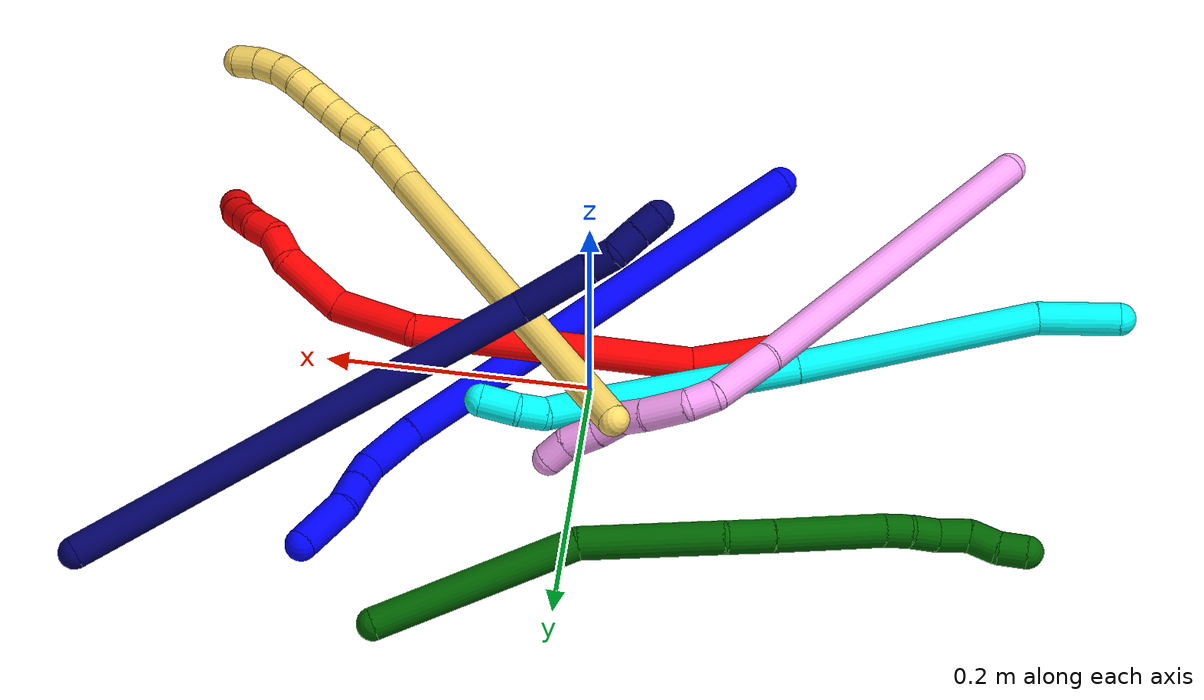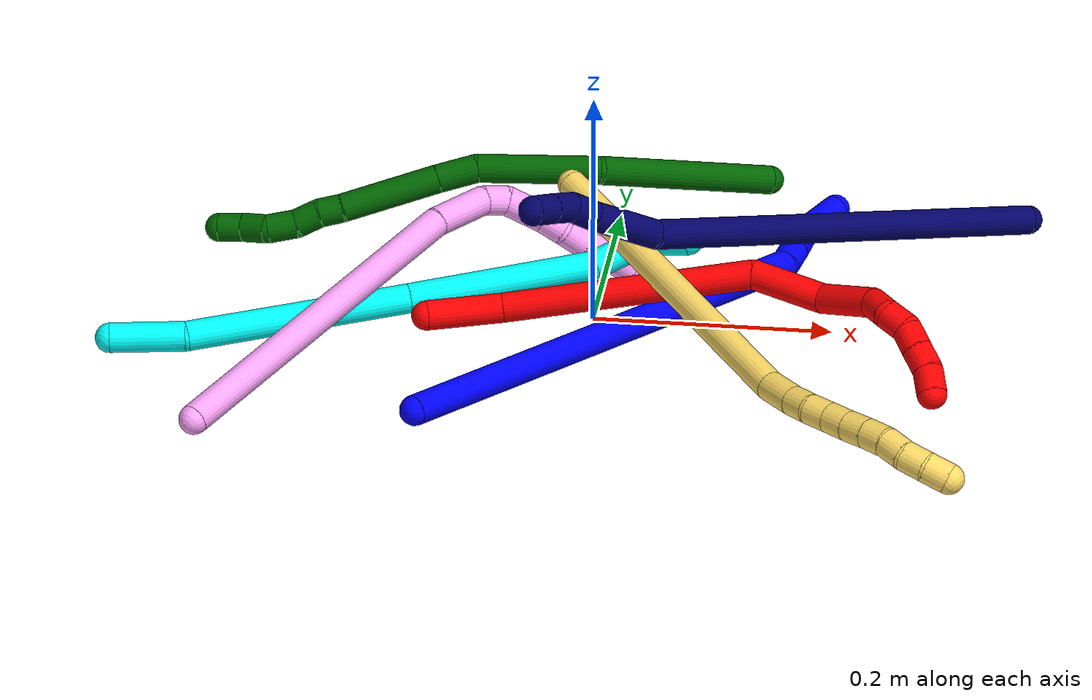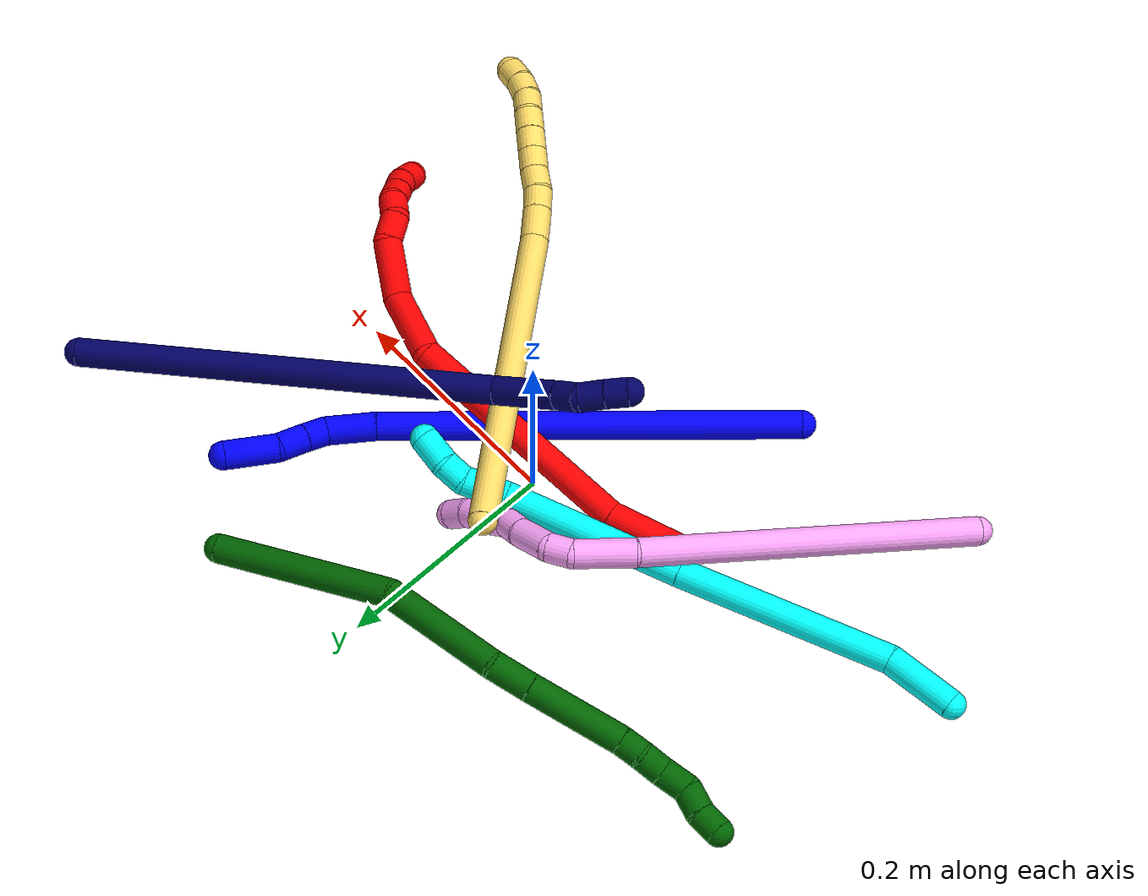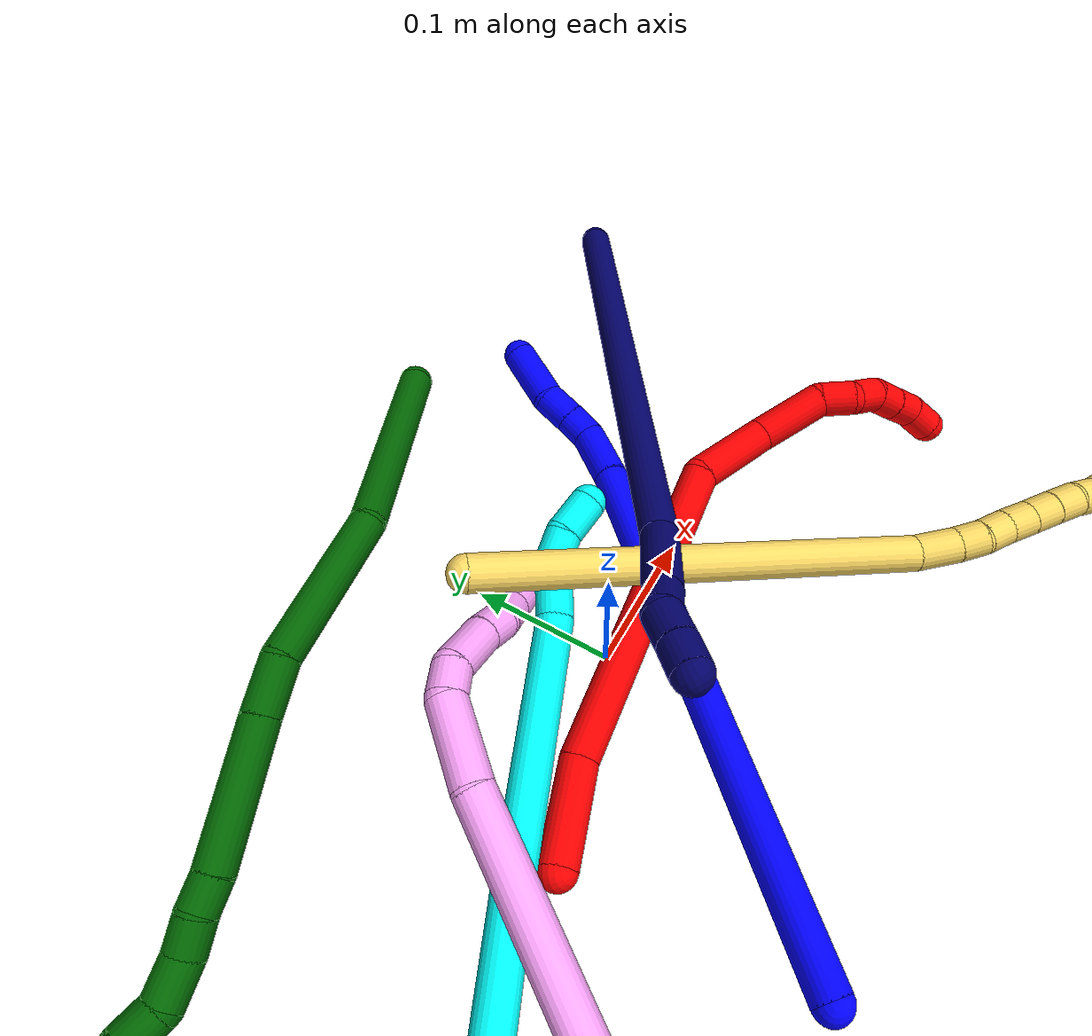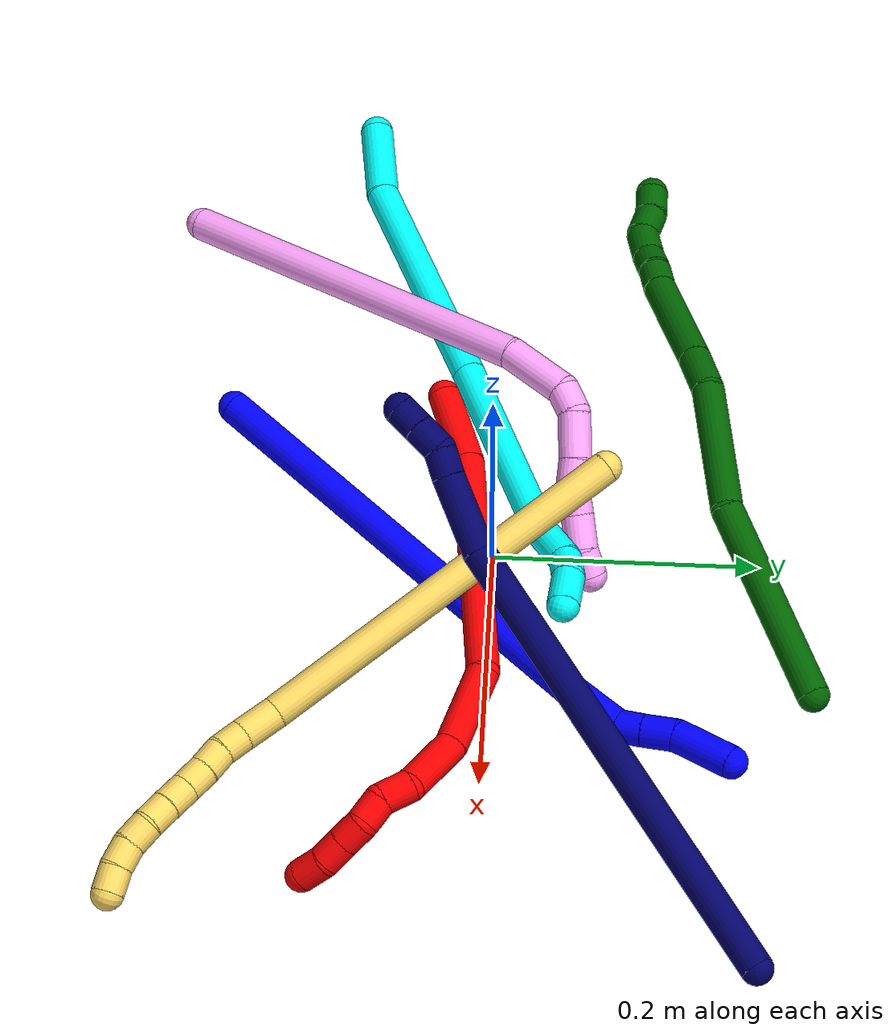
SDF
<sdf version="1.7">
 <world name="default">
  <plugin name="TubeGeneratorPlugin" filename="libtube_generator_plugin.so"/>
  <model name="photoneo_s_sensor">
   <static>1</static>
   <pose>0 0 2 1.57079 1.57079 3.14159</pose>
   <link name="link">
    <inertial><mass>0.1</mass></inertial>
    <sensor name="sensor" type="depth">
     <update_rate>30</update_rate>
     <camera>
      <horizontal_fov>1.22</horizontal_fov>
      <image><width>1920</width><height>1200</height><format>B8G8R8</format></image>
      <clip><near>0.1</near><far>4</far></clip>
      <depth_camera><output>points</output></depth_camera>
     </camera>
     <plugin name="camera_plugin" filename="libgazebo_ros_depth_camera.so">
      <baseline>0.2</baseline>
      <alwaysOn>1</alwaysOn>
      <updateRate>0.0</updateRate>
      <cameraName>camera_ir</cameraName>
      <imageTopicName>/camera/color/image_raw</imageTopicName>
      <cameraInfoTopicName>/camera/color/camera_info</cameraInfoTopicName>
      <depthImageTopicName>/camera/depth/image_raw</depthImageTopicName>
      <depthImageCameraInfoTopicName>/camera/depth/camera_info</depthImageCameraInfoTopicName>
      <pointCloudTopicName>/camera/depth/points</pointCloudTopicName>
      <frameName>fr_optical</frameName>
      <pointCloudCutoff>0.1</pointCloudCutoff>
      <pointCloudCutoffMax>2.0</pointCloudCutoffMax>
      <distortionK1>0</distortionK1>
      <distortionK2>0</distortionK2>
      <distortionK3>0</distortionK3>
      <distortionT1>0</distortionT1>
      <distortionT2>0</distortionT2>
      <CxPrime>0</CxPrime>
      <Cx>0</Cx>
      <Cy>0</Cy>
      <focalLength>0</focalLength>
      <hackBaseline>0</hackBaseline>
     </plugin>
    </sensor>
   </link>
  </model>
  <gravity>0 0 -9.8</gravity>
  <magnetic_field>6e-06 2.3e-05 -4.2e-05</magnetic_field>
  <atmosphere type="adiabatic"/>
  <physics name="default_physics" default="0" type="ode">
   <max_step_size>0.003</max_step_size>
   <real_time_factor>1</real_time_factor>
   <real_time_update_rate>1000</real_time_update_rate>
   <max_contacts>10000</max_contacts>
   <ode>
    <solver>
     <type>quick</type>
     <iters>100</iters>
     <sor>1.3</sor>
     <use_dynamic_moi_rescaling>0</use_dynamic_moi_rescaling>
    </solver>
    <constraints>
     <contact_max_correcting_vel>0</contact_max_correcting_vel>
     <contact_surface_layer>0.001</contact_surface_layer>
     <cfm>0</cfm>
     <erp>0.2</erp>
    </constraints>
   </ode>
  </physics>
  <scene><ambient>0.4 0.4 0.4 1</ambient><background>0.7 0.7 0.7 1</background><shadows>0</shadows></scene>
  <audio><device>default</device></audio>
  <spherical_coordinates>
   <surface_model>EARTH_WGS84</surface_model>
   <latitude_deg>0</latitude_deg>
   <longitude_deg>0</longitude_deg>
   <elevation>0</elevation>
   <heading_deg>0</heading_deg>
  </spherical_coordinates>
  <model name="bin">
   <static>1</static>
   <link name="bottom">
    <collision name="collision-bottom">
     <pose>0 0 -0.01 0 -0 0</pose>
     <geometry><box><size>0.8 0.6 0.02</size></box></geometry>
     <surface>
      <friction><ode><mu>100</mu><mu2>100</mu2></ode></friction>
      <contact><collide_bitmask>65535</collide_bitmask></contact>
     </surface>
    </collision>
   </link>
   <link name="west_wall">
    <collision name="collision-west_wall">
     <pose>-0.41 0 0.1 0 -0 0</pose>
     <geometry><box><size>0.02 0.6 0.2</size></box></geometry>
     <surface>
      <friction><ode><mu>100</mu><mu2>100</mu2></ode></friction>
      <contact><collide_bitmask>65535</collide_bitmask></contact>
     </surface>
    </collision>
   </link>
   <link name="east_wall">
    <collision name="collision-east_wall">
     <pose>0.41 0 0.1 0 -0 0</pose>
     <geometry><box><size>0.02 0.6 0.2</size></box></geometry>
     <surface>
      <friction><ode><mu>100</mu><mu2>100</mu2></ode></friction>
      <contact><collide_bitmask>65535</collide_bitmask></contact>
     </surface>
    </collision>
   </link>
   <link name="south_wall">
    <collision name="collision-south_wall">
     <pose>0 -0.31 0.1 0 -0 0</pose>
     <geometry><box><size>0.8 0.02 0.2</size></box></geometry>
     <surface>
      <friction><ode><mu>100</mu><mu2>100</mu2></ode></friction>
      <contact><collide_bitmask>65535</collide_bitmask></contact>
     </surface>
    </collision>
   </link>
   <link name="north_wall">
    <collision name="collision-north_wall">
     <pose>0 0.31 0.1 0 -0 0</pose>
     <geometry><box><size>0.8 0.02 0.2</size></box></geometry>
     <surface>
      <friction><ode><mu>100</mu><mu2>100</mu2></ode></friction>
      <contact><collide_bitmask>65535</collide_bitmask></contact>
     </surface>
    </collision>
   </link>
  </model>
  <model name="1">
   <static>0</static>
   <link name="1">
    <collision name="collision-cylinder-e_1_1_4">
     <pose>0.122902 0.132456 -0.017946 -1.70546 0.743468 -0.83945</pose>
     <geometry><cylinder><radius>0.0125</radius><length>0.363162</length></cylinder></geometry>
     <surface>
      <friction><ode><mu>1.16</mu><mu2>1.16</mu2><slip1>0</slip1><slip2>0</slip2></ode></friction>
      <contact><ode><kp>1e+06</kp><kd>1</kd><max_vel>0</max_vel><min_depth>0.001</min_depth></ode></contact>
     </surface>
    </collision>
    <visual name="visual-cylinder-e_1_1_4">
     <pose>0.122902 0.132456 -0.017946 -1.70546 0.743468 -0.83945</pose>
     <geometry><cylinder><radius>0.0125</radius><length>0.363162</length></cylinder></geometry>
     <material><ambient>0 0 1 1</ambient></material>
    </visual>
    <collision name="collision-cylinder-e_2_4_5">
     <pose>0.259202 0.281781 -0.039068 -1.7569 0.662747 -0.786546</pose>
     <geometry><cylinder><radius>0.0125</radius><length>0.043548</length></cylinder></geometry>
     <surface>
      <friction><ode><mu>1.16</mu><mu2>1.16</mu2><slip1>0</slip1><slip2>0</slip2></ode></friction>
      <contact><ode><kp>1e+06</kp><kd>1</kd><max_vel>0</max_vel><min_depth>0.001</min_depth></ode></contact>
     </surface>
    </collision>
    <visual name="visual-cylinder-e_2_4_5">
     <pose>0.259202 0.281781 -0.039068 -1.7569 0.662747 -0.786546</pose>
     <geometry><cylinder><radius>0.0125</radius><length>0.043548</length></cylinder></geometry>
     <material><ambient>0 0 1 1</ambient></material>
    </visual>
    <collision name="collision-cylinder-e_3_5_6">
     <pose>0.275672 0.308483 -0.041055 -1.45048 0.300837 -0.267088</pose>
     <geometry><cylinder><radius>0.0125</radius><length>0.020744</length></cylinder></geometry>
     <surface>
      <friction><ode><mu>1.16</mu><mu2>1.16</mu2><slip1>0</slip1><slip2>0</slip2></ode></friction>
      <contact><ode><kp>1e+06</kp><kd>1</kd><max_vel>0</max_vel><min_depth>0.001</min_depth></ode></contact>
     </surface>
    </collision>
    <visual name="visual-cylinder-e_3_5_6">
     <pose>0.275672 0.308483 -0.041055 -1.45048 0.300837 -0.267088</pose>
     <geometry><cylinder><radius>0.0125</radius><length>0.020744</length></cylinder></geometry>
     <material><ambient>0 0 1 1</ambient></material>
    </visual>
    <collision name="collision-cylinder-e_4_6_7">
     <pose>0.281954 0.330347 -0.03851 -1.45853 0.259066 -0.23176</pose>
     <geometry><cylinder><radius>0.0125</radius><length>0.025047</length></cylinder></geometry>
     <surface>
      <friction><ode><mu>1.16</mu><mu2>1.16</mu2><slip1>0</slip1><slip2>0</slip2></ode></friction>
      <contact><ode><kp>1e+06</kp><kd>1</kd><max_vel>0</max_vel><min_depth>0.001</min_depth></ode></contact>
     </surface>
    </collision>
    <visual name="visual-cylinder-e_4_6_7">
     <pose>0.281954 0.330347 -0.03851 -1.45853 0.259066 -0.23176</pose>
     <geometry><cylinder><radius>0.0125</radius><length>0.025047</length></cylinder></geometry>
     <material><ambient>0 0 1 1</ambient></material>
    </visual>
    <collision name="collision-cylinder-e_5_7_2">
     <pose>0.2975 0.36267 -0.037019 -1.56414 0.546259 -0.542812</pose>
     <geometry><cylinder><radius>0.0125</radius><length>0.047499</length></cylinder></geometry>
     <surface>
      <friction><ode><mu>1.16</mu><mu2>1.16</mu2><slip1>0</slip1><slip2>0</slip2></ode></friction>
      <contact><ode><kp>1e+06</kp><kd>1</kd><max_vel>0</max_vel><min_depth>0.001</min_depth></ode></contact>
     </surface>
    </collision>
    <visual name="visual-cylinder-e_5_7_2">
     <pose>0.2975 0.36267 -0.037019 -1.56414 0.546259 -0.542812</pose>
     <geometry><cylinder><radius>0.0125</radius><length>0.047499</length></cylinder></geometry>
     <material><ambient>0 0 1 1</ambient></material>
    </visual>
    <collision name="collision-sphere-2">
     <pose>0.309838 0.382962 -0.036884 0 -0 0</pose>
     <geometry><sphere><radius>0.0125</radius></sphere></geometry>
     <surface>
      <friction><ode><mu>1.16</mu><mu2>1.16</mu2><slip1>0</slip1><slip2>0</slip2></ode></friction>
      <contact><ode><kp>1e+06</kp><kd>1</kd><max_vel>0</max_vel><min_depth>0.001</min_depth></ode></contact>
     </surface>
    </collision>
    <visual name="visual-sphere-2">
     <pose>0.309838 0.382962 -0.036884 0 -0 0</pose>
     <geometry><sphere><radius>0.0125</radius></sphere></geometry>
     <material><ambient>0 0 1 1</ambient></material>
    </visual>
    <collision name="collision-sphere-7">
     <pose>0.285162 0.342377 -0.037154 0 -0 0</pose>
     <geometry><sphere><radius>0.0125</radius></sphere></geometry>
     <surface>
      <friction><ode><mu>1.16</mu><mu2>1.16</mu2><slip1>0</slip1><slip2>0</slip2></ode></friction>
      <contact><ode><kp>1e+06</kp><kd>1</kd><max_vel>0</max_vel><min_depth>0.001</min_depth></ode></contact>
     </surface>
    </collision>
    <visual name="visual-sphere-7">
     <pose>0.285162 0.342377 -0.037154 0 -0 0</pose>
     <geometry><sphere><radius>0.0125</radius></sphere></geometry>
     <material><ambient>0 0 1 1</ambient></material>
    </visual>
    <collision name="collision-sphere-6">
     <pose>0.278746 0.318318 -0.039866 0 -0 0</pose>
     <geometry><sphere><radius>0.0125</radius></sphere></geometry>
     <surface>
      <friction><ode><mu>1.16</mu><mu2>1.16</mu2><slip1>0</slip1><slip2>0</slip2></ode></friction>
      <contact><ode><kp>1e+06</kp><kd>1</kd><max_vel>0</max_vel><min_depth>0.001</min_depth></ode></contact>
     </surface>
    </collision>
    <visual name="visual-sphere-6">
     <pose>0.278746 0.318318 -0.039866 0 -0 0</pose>
     <geometry><sphere><radius>0.0125</radius></sphere></geometry>
     <material><ambient>0 0 1 1</ambient></material>
    </visual>
    <collision name="collision-sphere-5">
     <pose>0.272599 0.298649 -0.042244 0 -0 0</pose>
     <geometry><sphere><radius>0.0125</radius></sphere></geometry>
     <surface>
      <friction><ode><mu>1.16</mu><mu2>1.16</mu2><slip1>0</slip1><slip2>0</slip2></ode></friction>
      <contact><ode><kp>1e+06</kp><kd>1</kd><max_vel>0</max_vel><min_depth>0.001</min_depth></ode></contact>
     </surface>
    </collision>
    <visual name="visual-sphere-5">
     <pose>0.272599 0.298649 -0.042244 0 -0 0</pose>
     <geometry><sphere><radius>0.0125</radius></sphere></geometry>
     <material><ambient>0 0 1 1</ambient></material>
    </visual>
    <collision name="collision-sphere-1">
     <geometry><sphere><radius>0.0125</radius></sphere></geometry>
     <surface>
      <friction><ode><mu>1.16</mu><mu2>1.16</mu2><slip1>0</slip1><slip2>0</slip2></ode></friction>
      <contact><ode><kp>1e+06</kp><kd>1</kd><max_vel>0</max_vel><min_depth>0.001</min_depth></ode></contact>
     </surface>
    </collision>
    <visual name="visual-sphere-1">
     <geometry><sphere><radius>0.0125</radius></sphere></geometry>
     <material><ambient>0 0 1 1</ambient></material>
    </visual>
    <collision name="collision-sphere-4">
     <pose>0.245804 0.264912 -0.035892 0 -0 0</pose>
     <geometry><sphere><radius>0.0125</radius></sphere></geometry>
     <surface>
      <friction><ode><mu>1.16</mu><mu2>1.16</mu2><slip1>0</slip1><slip2>0</slip2></ode></friction>
      <contact><ode><kp>1e+06</kp><kd>1</kd><max_vel>0</max_vel><min_depth>0.001</min_depth></ode></contact>
     </surface>
    </collision>
    <visual name="visual-sphere-4">
     <pose>0.245804 0.264912 -0.035892 0 -0 0</pose>
     <geometry><sphere><radius>0.0125</radius></sphere></geometry>
     <material><ambient>0 0 1 1</ambient></material>
    </visual>
    <inertial>
     <pose>0.165665 0.184548 -0.023586 0 -0 0</pose>
     <mass>0.5</mass>
     <inertia>
      <ixx>-0.000195</ixx>
      <ixy>0</ixy>
      <ixz>0</ixz>
      <iyy>-0.000529</iyy>
      <iyz>0</iyz>
      <izz>-0.005667</izz>
     </inertia>
    </inertial>
   </link>
   <pose>-0.119265 -0.202807 0.011497 0.069731 -0.078074 0.006981</pose>
  </model>
  <model name="2">
   <static>0</static>
   <link name="2">
    <collision name="collision-cylinder-e_1_1_4">
     <pose>0.032264 0.00055 -0.001719 -2.83189 1.51493 -2.81439</pose>
     <geometry><cylinder><radius>0.0125</radius><length>0.064629</length></cylinder></geometry>
     <surface>
      <friction><ode><mu>1.16</mu><mu2>1.16</mu2><slip1>0</slip1><slip2>0</slip2></ode></friction>
      <contact><ode><kp>1e+06</kp><kd>1</kd><max_vel>0</max_vel><min_depth>0.001</min_depth></ode></contact>
     </surface>
    </collision>
    <visual name="visual-cylinder-e_1_1_4">
     <pose>0.032264 0.00055 -0.001719 -2.83189 1.51493 -2.81439</pose>
     <geometry><cylinder><radius>0.0125</radius><length>0.064629</length></cylinder></geometry>
     <material><ambient>1 0 0 1</ambient></material>
    </visual>
    <collision name="collision-cylinder-e_2_4_5">
     <pose>0.167679 0.000474 0.019483 0.027315 1.35207 0.02191</pose>
     <geometry><cylinder><radius>0.0125</radius><length>0.211338</length></cylinder></geometry>
     <surface>
      <friction><ode><mu>1.16</mu><mu2>1.16</mu2><slip1>0</slip1><slip2>0</slip2></ode></friction>
      <contact><ode><kp>1e+06</kp><kd>1</kd><max_vel>0</max_vel><min_depth>0.001</min_depth></ode></contact>
     </surface>
    </collision>
    <visual name="visual-cylinder-e_2_4_5">
     <pose>0.167679 0.000474 0.019483 0.027315 1.35207 0.02191</pose>
     <geometry><cylinder><radius>0.0125</radius><length>0.211338</length></cylinder></geometry>
     <material><ambient>1 0 0 1</ambient></material>
    </visual>
    <collision name="collision-cylinder-e_3_5_6">
     <pose>0.296552 -0.01533 0.053422 0.942866 0.94077 0.507223</pose>
     <geometry><cylinder><radius>0.0125</radius><length>0.063665</length></cylinder></geometry>
     <surface>
      <friction><ode><mu>1.16</mu><mu2>1.16</mu2><slip1>0</slip1><slip2>0</slip2></ode></friction>
      <contact><ode><kp>1e+06</kp><kd>1</kd><max_vel>0</max_vel><min_depth>0.001</min_depth></ode></contact>
     </surface>
    </collision>
    <visual name="visual-cylinder-e_3_5_6">
     <pose>0.296552 -0.01533 0.053422 0.942866 0.94077 0.507223</pose>
     <geometry><cylinder><radius>0.0125</radius><length>0.063665</length></cylinder></geometry>
     <material><ambient>1 0 0 1</ambient></material>
    </visual>
    <collision name="collision-cylinder-e_4_6_7">
     <pose>0.339345 -0.037839 0.082935 0.377441 0.709159 0.141187</pose>
     <geometry><cylinder><radius>0.0125</radius><length>0.052433</length></cylinder></geometry>
     <surface>
      <friction><ode><mu>1.16</mu><mu2>1.16</mu2><slip1>0</slip1><slip2>0</slip2></ode></friction>
      <contact><ode><kp>1e+06</kp><kd>1</kd><max_vel>0</max_vel><min_depth>0.001</min_depth></ode></contact>
     </surface>
    </collision>
    <visual name="visual-cylinder-e_4_6_7">
     <pose>0.339345 -0.037839 0.082935 0.377441 0.709159 0.141187</pose>
     <geometry><cylinder><radius>0.0125</radius><length>0.052433</length></cylinder></geometry>
     <material><ambient>1 0 0 1</ambient></material>
    </visual>
    <collision name="collision-cylinder-e_5_7_8">
     <pose>0.359954 -0.052384 0.110709 0.660773 0.292368 0.100904</pose>
     <geometry><cylinder><radius>0.0125</radius><length>0.024546</length></cylinder></geometry>
     <surface>
      <friction><ode><mu>1.16</mu><mu2>1.16</mu2><slip1>0</slip1><slip2>0</slip2></ode></friction>
      <contact><ode><kp>1e+06</kp><kd>1</kd><max_vel>0</max_vel><min_depth>0.001</min_depth></ode></contact>
     </surface>
    </collision>
    <visual name="visual-cylinder-e_5_7_8">
     <pose>0.359954 -0.052384 0.110709 0.660773 0.292368 0.100904</pose>
     <geometry><cylinder><radius>0.0125</radius><length>0.024546</length></cylinder></geometry>
     <material><ambient>1 0 0 1</ambient></material>
    </visual>
    <collision name="collision-cylinder-e_6_8_9">
     <pose>0.369758 -0.067067 0.124319 1.04526 0.627809 0.369752</pose>
     <geometry><cylinder><radius>0.0125</radius><length>0.02134</length></cylinder></geometry>
     <surface>
      <friction><ode><mu>1.16</mu><mu2>1.16</mu2><slip1>0</slip1><slip2>0</slip2></ode></friction>
      <contact><ode><kp>1e+06</kp><kd>1</kd><max_vel>0</max_vel><min_depth>0.001</min_depth></ode></contact>
     </surface>
    </collision>
    <visual name="visual-cylinder-e_6_8_9">
     <pose>0.369758 -0.067067 0.124319 1.04526 0.627809 0.369752</pose>
     <geometry><cylinder><radius>0.0125</radius><length>0.02134</length></cylinder></geometry>
     <material><ambient>1 0 0 1</ambient></material>
    </visual>
    <collision name="collision-cylinder-e_7_9_10">
     <pose>0.378635 -0.083928 0.13117 1.30882 0.262225 0.201649</pose>
     <geometry><cylinder><radius>0.0125</radius><length>0.020133</length></cylinder></geometry>
     <surface>
      <friction><ode><mu>1.16</mu><mu2>1.16</mu2><slip1>0</slip1><slip2>0</slip2></ode></friction>
      <contact><ode><kp>1e+06</kp><kd>1</kd><max_vel>0</max_vel><min_depth>0.001</min_depth></ode></contact>
     </surface>
    </collision>
    <visual name="visual-cylinder-e_7_9_10">
     <pose>0.378635 -0.083928 0.13117 1.30882 0.262225 0.201649</pose>
     <geometry><cylinder><radius>0.0125</radius><length>0.020133</length></cylinder></geometry>
     <material><ambient>1 0 0 1</ambient></material>
    </visual>
    <collision name="collision-cylinder-e_8_10_11">
     <pose>0.384128 -0.102696 0.136185 1.31057 0.28881 0.222605</pose>
     <geometry><cylinder><radius>0.0125</radius><length>0.020247</length></cylinder></geometry>
     <surface>
      <friction><ode><mu>1.16</mu><mu2>1.16</mu2><slip1>0</slip1><slip2>0</slip2></ode></friction>
      <contact><ode><kp>1e+06</kp><kd>1</kd><max_vel>0</max_vel><min_depth>0.001</min_depth></ode></contact>
     </surface>
    </collision>
    <visual name="visual-cylinder-e_8_10_11">
     <pose>0.384128 -0.102696 0.136185 1.31057 0.28881 0.222605</pose>
     <geometry><cylinder><radius>0.0125</radius><length>0.020247</length></cylinder></geometry>
     <material><ambient>1 0 0 1</ambient></material>
    </visual>
    <collision name="collision-cylinder-e_9_11_2">
     <pose>0.386904 -0.122623 0.14115 1.34096 -0.009921 -0.007868</pose>
     <geometry><cylinder><radius>0.0125</radius><length>0.02167</length></cylinder></geometry>
     <surface>
      <friction><ode><mu>1.16</mu><mu2>1.16</mu2><slip1>0</slip1><slip2>0</slip2></ode></friction>
      <contact><ode><kp>1e+06</kp><kd>1</kd><max_vel>0</max_vel><min_depth>0.001</min_depth></ode></contact>
     </surface>
    </collision>
    <visual name="visual-cylinder-e_9_11_2">
     <pose>0.386904 -0.122623 0.14115 1.34096 -0.009921 -0.007868</pose>
     <geometry><cylinder><radius>0.0125</radius><length>0.02167</length></cylinder></geometry>
     <material><ambient>1 0 0 1</ambient></material>
    </visual>
    <collision name="collision-sphere-2">
     <pose>0.386796 -0.133172 0.143618 0 -0 0</pose>
     <geometry><sphere><radius>0.0125</radius></sphere></geometry>
     <surface>
      <friction><ode><mu>1.16</mu><mu2>1.16</mu2><slip1>0</slip1><slip2>0</slip2></ode></friction>
      <contact><ode><kp>1e+06</kp><kd>1</kd><max_vel>0</max_vel><min_depth>0.001</min_depth></ode></contact>
     </surface>
    </collision>
    <visual name="visual-sphere-2">
     <pose>0.386796 -0.133172 0.143618 0 -0 0</pose>
     <geometry><sphere><radius>0.0125</radius></sphere></geometry>
     <material><ambient>1 0 0 1</ambient></material>
    </visual>
    <collision name="collision-sphere-11">
     <pose>0.387011 -0.112073 0.138681 0 -0 0</pose>
     <geometry><sphere><radius>0.0125</radius></sphere></geometry>
     <surface>
      <friction><ode><mu>1.16</mu><mu2>1.16</mu2><slip1>0</slip1><slip2>0</slip2></ode></friction>
      <contact><ode><kp>1e+06</kp><kd>1</kd><max_vel>0</max_vel><min_depth>0.001</min_depth></ode></contact>
     </surface>
    </collision>
    <visual name="visual-sphere-11">
     <pose>0.387011 -0.112073 0.138681 0 -0 0</pose>
     <geometry><sphere><radius>0.0125</radius></sphere></geometry>
     <material><ambient>1 0 0 1</ambient></material>
    </visual>
    <collision name="collision-sphere-10">
     <pose>0.381245 -0.093318 0.133688 0 -0 0</pose>
     <geometry><sphere><radius>0.0125</radius></sphere></geometry>
     <surface>
      <friction><ode><mu>1.16</mu><mu2>1.16</mu2><slip1>0</slip1><slip2>0</slip2></ode></friction>
      <contact><ode><kp>1e+06</kp><kd>1</kd><max_vel>0</max_vel><min_depth>0.001</min_depth></ode></contact>
     </surface>
    </collision>
    <visual name="visual-sphere-10">
     <pose>0.381245 -0.093318 0.133688 0 -0 0</pose>
     <geometry><sphere><radius>0.0125</radius></sphere></geometry>
     <material><ambient>1 0 0 1</ambient></material>
    </visual>
    <collision name="collision-sphere-9">
     <pose>0.376026 -0.074537 0.128651 0 -0 0</pose>
     <geometry><sphere><radius>0.0125</radius></sphere></geometry>
     <surface>
      <friction><ode><mu>1.16</mu><mu2>1.16</mu2><slip1>0</slip1><slip2>0</slip2></ode></friction>
      <contact><ode><kp>1e+06</kp><kd>1</kd><max_vel>0</max_vel><min_depth>0.001</min_depth></ode></contact>
     </surface>
    </collision>
    <visual name="visual-sphere-9">
     <pose>0.376026 -0.074537 0.128651 0 -0 0</pose>
     <geometry><sphere><radius>0.0125</radius></sphere></geometry>
     <material><ambient>1 0 0 1</ambient></material>
    </visual>
    <collision name="collision-sphere-4">
     <pose>0.064528 0.0011 -0.003437 0 -0 0</pose>
     <geometry><sphere><radius>0.0125</radius></sphere></geometry>
     <surface>
      <friction><ode><mu>1.16</mu><mu2>1.16</mu2><slip1>0</slip1><slip2>0</slip2></ode></friction>
      <contact><ode><kp>1e+06</kp><kd>1</kd><max_vel>0</max_vel><min_depth>0.001</min_depth></ode></contact>
     </surface>
    </collision>
    <visual name="visual-sphere-4">
     <pose>0.064528 0.0011 -0.003437 0 -0 0</pose>
     <geometry><sphere><radius>0.0125</radius></sphere></geometry>
     <material><ambient>1 0 0 1</ambient></material>
    </visual>
    <collision name="collision-sphere-1">
     <geometry><sphere><radius>0.0125</radius></sphere></geometry>
     <surface>
      <friction><ode><mu>1.16</mu><mu2>1.16</mu2><slip1>0</slip1><slip2>0</slip2></ode></friction>
      <contact><ode><kp>1e+06</kp><kd>1</kd><max_vel>0</max_vel><min_depth>0.001</min_depth></ode></contact>
     </surface>
    </collision>
    <visual name="visual-sphere-1">
     <geometry><sphere><radius>0.0125</radius></sphere></geometry>
     <material><ambient>1 0 0 1</ambient></material>
    </visual>
    <collision name="collision-sphere-8">
     <pose>0.363491 -0.059597 0.119987 0 -0 0</pose>
     <geometry><sphere><radius>0.0125</radius></sphere></geometry>
     <surface>
      <friction><ode><mu>1.16</mu><mu2>1.16</mu2><slip1>0</slip1><slip2>0</slip2></ode></friction>
      <contact><ode><kp>1e+06</kp><kd>1</kd><max_vel>0</max_vel><min_depth>0.001</min_depth></ode></contact>
     </surface>
    </collision>
    <visual name="visual-sphere-8">
     <pose>0.363491 -0.059597 0.119987 0 -0 0</pose>
     <geometry><sphere><radius>0.0125</radius></sphere></geometry>
     <material><ambient>1 0 0 1</ambient></material>
    </visual>
    <collision name="collision-sphere-5">
     <pose>0.270831 -0.000153 0.042404 0 -0 0</pose>
     <geometry><sphere><radius>0.0125</radius></sphere></geometry>
     <surface>
      <friction><ode><mu>1.16</mu><mu2>1.16</mu2><slip1>0</slip1><slip2>0</slip2></ode></friction>
      <contact><ode><kp>1e+06</kp><kd>1</kd><max_vel>0</max_vel><min_depth>0.001</min_depth></ode></contact>
     </surface>
    </collision>
    <visual name="visual-sphere-5">
     <pose>0.270831 -0.000153 0.042404 0 -0 0</pose>
     <geometry><sphere><radius>0.0125</radius></sphere></geometry>
     <material><ambient>1 0 0 1</ambient></material>
    </visual>
    <collision name="collision-sphere-6">
     <pose>0.322272 -0.030506 0.064439 0 -0 0</pose>
     <geometry><sphere><radius>0.0125</radius></sphere></geometry>
     <surface>
      <friction><ode><mu>1.16</mu><mu2>1.16</mu2><slip1>0</slip1><slip2>0</slip2></ode></friction>
      <contact><ode><kp>1e+06</kp><kd>1</kd><max_vel>0</max_vel><min_depth>0.001</min_depth></ode></contact>
     </surface>
    </collision>
    <visual name="visual-sphere-6">
     <pose>0.322272 -0.030506 0.064439 0 -0 0</pose>
     <geometry><sphere><radius>0.0125</radius></sphere></geometry>
     <material><ambient>1 0 0 1</ambient></material>
    </visual>
    <collision name="collision-sphere-7">
     <pose>0.356417 -0.045172 0.10143 0 -0 0</pose>
     <geometry><sphere><radius>0.0125</radius></sphere></geometry>
     <surface>
      <friction><ode><mu>1.16</mu><mu2>1.16</mu2><slip1>0</slip1><slip2>0</slip2></ode></friction>
      <contact><ode><kp>1e+06</kp><kd>1</kd><max_vel>0</max_vel><min_depth>0.001</min_depth></ode></contact>
     </surface>
    </collision>
    <visual name="visual-sphere-7">
     <pose>0.356417 -0.045172 0.10143 0 -0 0</pose>
     <geometry><sphere><radius>0.0125</radius></sphere></geometry>
     <material><ambient>1 0 0 1</ambient></material>
    </visual>
    <inertial>
     <pose>0.229411 -0.023935 0.051167 0 -0 0</pose>
     <mass>0.5</mass>
     <inertia>
      <ixx>0.000245</ixx>
      <ixy>0</ixy>
      <ixz>0</ixz>
      <iyy>0.00086</iyy>
      <iyz>0</iyz>
      <izz>-0.000794</izz>
     </inertia>
    </inertial>
   </link>
   <pose>-0.134701 -0.04296 0.01578 0.896339 -0.02807 0.27967</pose>
  </model>
  <model name="3">
   <static>0</static>
   <link name="3">
    <collision name="collision-cylinder-e_1_1_4">
     <pose>0.020303 0.013776 -0.019607 -2.52911 0.702899 -1.71839</pose>
     <geometry><cylinder><radius>0.0125</radius><length>0.062815</length></cylinder></geometry>
     <surface>
      <friction><ode><mu>1.16</mu><mu2>1.16</mu2><slip1>0</slip1><slip2>0</slip2></ode></friction>
      <contact><ode><kp>1e+06</kp><kd>1</kd><max_vel>0</max_vel><min_depth>0.001</min_depth></ode></contact>
     </surface>
    </collision>
    <visual name="visual-cylinder-e_1_1_4">
     <pose>0.020303 0.013776 -0.019607 -2.52911 0.702899 -1.71839</pose>
     <geometry><cylinder><radius>0.0125</radius><length>0.062815</length></cylinder></geometry>
     <material><ambient>0.003922 1 0.996078 1</ambient></material>
    </visual>
    <collision name="collision-cylinder-e_2_4_5">
     <pose>0.091919 0.051218 -0.115564 -2.84102 0.570694 -2.18856</pose>
     <geometry><cylinder><radius>0.0125</radius><length>0.189973</length></cylinder></geometry>
     <surface>
      <friction><ode><mu>1.16</mu><mu2>1.16</mu2><slip1>0</slip1><slip2>0</slip2></ode></friction>
      <contact><ode><kp>1e+06</kp><kd>1</kd><max_vel>0</max_vel><min_depth>0.001</min_depth></ode></contact>
     </surface>
    </collision>
    <visual name="visual-cylinder-e_2_4_5">
     <pose>0.091919 0.051218 -0.115564 -2.84102 0.570694 -2.18856</pose>
     <geometry><cylinder><radius>0.0125</radius><length>0.189973</length></cylinder></geometry>
     <material><ambient>0.003922 1 0.996078 1</ambient></material>
    </visual>
    <collision name="collision-cylinder-e_3_5_6">
     <pose>0.185894 0.097019 -0.255697 -2.80756 0.563539 -2.08684</pose>
     <geometry><cylinder><radius>0.0125</radius><length>0.159727</length></cylinder></geometry>
     <surface>
      <friction><ode><mu>1.16</mu><mu2>1.16</mu2><slip1>0</slip1><slip2>0</slip2></ode></friction>
      <contact><ode><kp>1e+06</kp><kd>1</kd><max_vel>0</max_vel><min_depth>0.001</min_depth></ode></contact>
     </surface>
    </collision>
    <visual name="visual-cylinder-e_3_5_6">
     <pose>0.185894 0.097019 -0.255697 -2.80756 0.563539 -2.08684</pose>
     <geometry><cylinder><radius>0.0125</radius><length>0.159727</length></cylinder></geometry>
     <material><ambient>0.003922 1 0.996078 1</ambient></material>
    </visual>
    <collision name="collision-cylinder-e_4_6_7">
     <pose>0.234451 0.124152 -0.337147 -2.86589 0.310711 -1.69175</pose>
     <geometry><cylinder><radius>0.0125</radius><length>0.038568</length></cylinder></geometry>
     <surface>
      <friction><ode><mu>1.16</mu><mu2>1.16</mu2><slip1>0</slip1><slip2>0</slip2></ode></friction>
      <contact><ode><kp>1e+06</kp><kd>1</kd><max_vel>0</max_vel><min_depth>0.001</min_depth></ode></contact>
     </surface>
    </collision>
    <visual name="visual-cylinder-e_4_6_7">
     <pose>0.234451 0.124152 -0.337147 -2.86589 0.310711 -1.69175</pose>
     <geometry><cylinder><radius>0.0125</radius><length>0.038568</length></cylinder></geometry>
     <material><ambient>0.003922 1 0.996078 1</ambient></material>
    </visual>
    <collision name="collision-cylinder-e_5_7_8">
     <pose>0.244693 0.135102 -0.362186 -2.46236 0.430065 -1.10738</pose>
     <geometry><cylinder><radius>0.0125</radius><length>0.020849</length></cylinder></geometry>
     <surface>
      <friction><ode><mu>1.16</mu><mu2>1.16</mu2><slip1>0</slip1><slip2>0</slip2></ode></friction>
      <contact><ode><kp>1e+06</kp><kd>1</kd><max_vel>0</max_vel><min_depth>0.001</min_depth></ode></contact>
     </surface>
    </collision>
    <visual name="visual-cylinder-e_5_7_8">
     <pose>0.244693 0.135102 -0.362186 -2.46236 0.430065 -1.10738</pose>
     <geometry><cylinder><radius>0.0125</radius><length>0.020849</length></cylinder></geometry>
     <material><ambient>0.003922 1 0.996078 1</ambient></material>
    </visual>
    <collision name="collision-cylinder-e_6_8_2">
     <pose>0.2577 0.149877 -0.3762 -2.2161 0.66511 -1.21111</pose>
     <geometry><cylinder><radius>0.0125</radius><length>0.028068</length></cylinder></geometry>
     <surface>
      <friction><ode><mu>1.16</mu><mu2>1.16</mu2><slip1>0</slip1><slip2>0</slip2></ode></friction>
      <contact><ode><kp>1e+06</kp><kd>1</kd><max_vel>0</max_vel><min_depth>0.001</min_depth></ode></contact>
     </surface>
    </collision>
    <visual name="visual-cylinder-e_6_8_2">
     <pose>0.2577 0.149877 -0.3762 -2.2161 0.66511 -1.21111</pose>
     <geometry><cylinder><radius>0.0125</radius><length>0.028068</length></cylinder></geometry>
     <material><ambient>0.003922 1 0.996078 1</ambient></material>
    </visual>
    <collision name="collision-sphere-2">
     <pose>0.266362 0.158699 -0.382841 0 -0 0</pose>
     <geometry><sphere><radius>0.0125</radius></sphere></geometry>
     <surface>
      <friction><ode><mu>1.16</mu><mu2>1.16</mu2><slip1>0</slip1><slip2>0</slip2></ode></friction>
      <contact><ode><kp>1e+06</kp><kd>1</kd><max_vel>0</max_vel><min_depth>0.001</min_depth></ode></contact>
     </surface>
    </collision>
    <visual name="visual-sphere-2">
     <pose>0.266362 0.158699 -0.382841 0 -0 0</pose>
     <geometry><sphere><radius>0.0125</radius></sphere></geometry>
     <material><ambient>0.003922 1 0.996078 1</ambient></material>
    </visual>
    <collision name="collision-sphere-4">
     <pose>0.040606 0.027553 -0.039214 0 -0 0</pose>
     <geometry><sphere><radius>0.0125</radius></sphere></geometry>
     <surface>
      <friction><ode><mu>1.16</mu><mu2>1.16</mu2><slip1>0</slip1><slip2>0</slip2></ode></friction>
      <contact><ode><kp>1e+06</kp><kd>1</kd><max_vel>0</max_vel><min_depth>0.001</min_depth></ode></contact>
     </surface>
    </collision>
    <visual name="visual-sphere-4">
     <pose>0.040606 0.027553 -0.039214 0 -0 0</pose>
     <geometry><sphere><radius>0.0125</radius></sphere></geometry>
     <material><ambient>0.003922 1 0.996078 1</ambient></material>
    </visual>
    <collision name="collision-sphere-1">
     <geometry><sphere><radius>0.0125</radius></sphere></geometry>
     <surface>
      <friction><ode><mu>1.16</mu><mu2>1.16</mu2><slip1>0</slip1><slip2>0</slip2></ode></friction>
      <contact><ode><kp>1e+06</kp><kd>1</kd><max_vel>0</max_vel><min_depth>0.001</min_depth></ode></contact>
     </surface>
    </collision>
    <visual name="visual-sphere-1">
     <geometry><sphere><radius>0.0125</radius></sphere></geometry>
     <material><ambient>0.003922 1 0.996078 1</ambient></material>
    </visual>
    <collision name="collision-sphere-8">
     <pose>0.249039 0.141054 -0.369558 0 -0 0</pose>
     <geometry><sphere><radius>0.0125</radius></sphere></geometry>
     <surface>
      <friction><ode><mu>1.16</mu><mu2>1.16</mu2><slip1>0</slip1><slip2>0</slip2></ode></friction>
      <contact><ode><kp>1e+06</kp><kd>1</kd><max_vel>0</max_vel><min_depth>0.001</min_depth></ode></contact>
     </surface>
    </collision>
    <visual name="visual-sphere-8">
     <pose>0.249039 0.141054 -0.369558 0 -0 0</pose>
     <geometry><sphere><radius>0.0125</radius></sphere></geometry>
     <material><ambient>0.003922 1 0.996078 1</ambient></material>
    </visual>
    <collision name="collision-sphere-5">
     <pose>0.143232 0.074884 -0.191914 0 -0 0</pose>
     <geometry><sphere><radius>0.0125</radius></sphere></geometry>
     <surface>
      <friction><ode><mu>1.16</mu><mu2>1.16</mu2><slip1>0</slip1><slip2>0</slip2></ode></friction>
      <contact><ode><kp>1e+06</kp><kd>1</kd><max_vel>0</max_vel><min_depth>0.001</min_depth></ode></contact>
     </surface>
    </collision>
    <visual name="visual-sphere-5">
     <pose>0.143232 0.074884 -0.191914 0 -0 0</pose>
     <geometry><sphere><radius>0.0125</radius></sphere></geometry>
     <material><ambient>0.003922 1 0.996078 1</ambient></material>
    </visual>
    <collision name="collision-sphere-6">
     <pose>0.228555 0.119154 -0.319479 0 -0 0</pose>
     <geometry><sphere><radius>0.0125</radius></sphere></geometry>
     <surface>
      <friction><ode><mu>1.16</mu><mu2>1.16</mu2><slip1>0</slip1><slip2>0</slip2></ode></friction>
      <contact><ode><kp>1e+06</kp><kd>1</kd><max_vel>0</max_vel><min_depth>0.001</min_depth></ode></contact>
     </surface>
    </collision>
    <visual name="visual-sphere-6">
     <pose>0.228555 0.119154 -0.319479 0 -0 0</pose>
     <geometry><sphere><radius>0.0125</radius></sphere></geometry>
     <material><ambient>0.003922 1 0.996078 1</ambient></material>
    </visual>
    <collision name="collision-sphere-7">
     <pose>0.240347 0.12915 -0.354814 0 -0 0</pose>
     <geometry><sphere><radius>0.0125</radius></sphere></geometry>
     <surface>
      <friction><ode><mu>1.16</mu><mu2>1.16</mu2><slip1>0</slip1><slip2>0</slip2></ode></friction>
      <contact><ode><kp>1e+06</kp><kd>1</kd><max_vel>0</max_vel><min_depth>0.001</min_depth></ode></contact>
     </surface>
    </collision>
    <visual name="visual-sphere-7">
     <pose>0.240347 0.12915 -0.354814 0 -0 0</pose>
     <geometry><sphere><radius>0.0125</radius></sphere></geometry>
     <material><ambient>0.003922 1 0.996078 1</ambient></material>
    </visual>
    <inertial>
     <pose>0.139613 0.075807 -0.190282 0 -0 0</pose>
     <mass>0.5</mass>
     <inertia>
      <ixx>-0.001086</ixx>
      <ixy>0</ixy>
      <ixz>0</ixz>
      <iyy>-4.3e-05</iyy>
      <iyz>0</iyz>
      <izz>-0.000801</izz>
     </inertia>
    </inertial>
   </link>
   <pose>-0.388506 -0.109882 0.012505 2.08521 0.796299 -0.202183</pose>
  </model>
  <model name="4">
   <static>0</static>
   <link name="4">
    <collision name="collision-cylinder-e_1_1_4">
     <pose>0.00531 0.006371 -0.150748 -3.09935 0.035176 -1.38877</pose>
     <geometry><cylinder><radius>0.0125</radius><length>0.301951</length></cylinder></geometry>
     <surface>
      <friction><ode><mu>1.16</mu><mu2>1.16</mu2><slip1>0</slip1><slip2>0</slip2></ode></friction>
      <contact><ode><kp>1e+06</kp><kd>1</kd><max_vel>0</max_vel><min_depth>0.001</min_depth></ode></contact>
     </surface>
    </collision>
    <visual name="visual-cylinder-e_1_1_4">
     <pose>0.00531 0.006371 -0.150748 -3.09935 0.035176 -1.38877</pose>
     <geometry><cylinder><radius>0.0125</radius><length>0.301951</length></cylinder></geometry>
     <material><ambient>1 0.65098 0.996078 1</ambient></material>
    </visual>
    <collision name="collision-cylinder-e_2_4_5">
     <pose>0.016843 0.01461 -0.326981 -3.06845 0.238904 -2.54985</pose>
     <geometry><cylinder><radius>0.0125</radius><length>0.052603</length></cylinder></geometry>
     <surface>
      <friction><ode><mu>1.16</mu><mu2>1.16</mu2><slip1>0</slip1><slip2>0</slip2></ode></friction>
      <contact><ode><kp>1e+06</kp><kd>1</kd><max_vel>0</max_vel><min_depth>0.001</min_depth></ode></contact>
     </surface>
    </collision>
    <visual name="visual-cylinder-e_2_4_5">
     <pose>0.016843 0.01461 -0.326981 -3.06845 0.238904 -2.54985</pose>
     <geometry><cylinder><radius>0.0125</radius><length>0.052603</length></cylinder></geometry>
     <material><ambient>1 0.65098 0.996078 1</ambient></material>
    </visual>
    <collision name="collision-cylinder-e_3_5_6">
     <pose>0.029165 0.01962 -0.360471 -2.76744 0.616851 -2.06939</pose>
     <geometry><cylinder><radius>0.0125</radius><length>0.021082</length></cylinder></geometry>
     <surface>
      <friction><ode><mu>1.16</mu><mu2>1.16</mu2><slip1>0</slip1><slip2>0</slip2></ode></friction>
      <contact><ode><kp>1e+06</kp><kd>1</kd><max_vel>0</max_vel><min_depth>0.001</min_depth></ode></contact>
     </surface>
    </collision>
    <visual name="visual-cylinder-e_3_5_6">
     <pose>0.029165 0.01962 -0.360471 -2.76744 0.616851 -2.06939</pose>
     <geometry><cylinder><radius>0.0125</radius><length>0.021082</length></cylinder></geometry>
     <material><ambient>1 0.65098 0.996078 1</ambient></material>
    </visual>
    <collision name="collision-cylinder-e_4_6_7">
     <pose>0.050365 0.028869 -0.375184 -2.40321 1.02986 -1.94203</pose>
     <geometry><cylinder><radius>0.0125</radius><length>0.035237</length></cylinder></geometry>
     <surface>
      <friction><ode><mu>1.16</mu><mu2>1.16</mu2><slip1>0</slip1><slip2>0</slip2></ode></friction>
      <contact><ode><kp>1e+06</kp><kd>1</kd><max_vel>0</max_vel><min_depth>0.001</min_depth></ode></contact>
     </surface>
    </collision>
    <visual name="visual-cylinder-e_4_6_7">
     <pose>0.050365 0.028869 -0.375184 -2.40321 1.02986 -1.94203</pose>
     <geometry><cylinder><radius>0.0125</radius><length>0.035237</length></cylinder></geometry>
     <material><ambient>1 0.65098 0.996078 1</ambient></material>
    </visual>
    <collision name="collision-cylinder-e_5_7_8">
     <pose>0.074494 0.038793 -0.384338 -2.14032 1.10536 -1.69036</pose>
     <geometry><cylinder><radius>0.0125</radius><length>0.020201</length></cylinder></geometry>
     <surface>
      <friction><ode><mu>1.16</mu><mu2>1.16</mu2><slip1>0</slip1><slip2>0</slip2></ode></friction>
      <contact><ode><kp>1e+06</kp><kd>1</kd><max_vel>0</max_vel><min_depth>0.001</min_depth></ode></contact>
     </surface>
    </collision>
    <visual name="visual-cylinder-e_5_7_8">
     <pose>0.074494 0.038793 -0.384338 -2.14032 1.10536 -1.69036</pose>
     <geometry><cylinder><radius>0.0125</radius><length>0.020201</length></cylinder></geometry>
     <material><ambient>1 0.65098 0.996078 1</ambient></material>
    </visual>
    <collision name="collision-cylinder-e_6_8_9">
     <pose>0.093485 0.043729 -0.391181 -2.89271 1.14343 -2.75755</pose>
     <geometry><cylinder><radius>0.0125</radius><length>0.021899</length></cylinder></geometry>
     <surface>
      <friction><ode><mu>1.16</mu><mu2>1.16</mu2><slip1>0</slip1><slip2>0</slip2></ode></friction>
      <contact><ode><kp>1e+06</kp><kd>1</kd><max_vel>0</max_vel><min_depth>0.001</min_depth></ode></contact>
     </surface>
    </collision>
    <visual name="visual-cylinder-e_6_8_9">
     <pose>0.093485 0.043729 -0.391181 -2.89271 1.14343 -2.75755</pose>
     <geometry><cylinder><radius>0.0125</radius><length>0.021899</length></cylinder></geometry>
     <material><ambient>1 0.65098 0.996078 1</ambient></material>
    </visual>
    <collision name="collision-cylinder-e_7_9_10">
     <pose>0.115065 0.048017 -0.401337 -2.63825 1.05584 -2.311</pose>
     <geometry><cylinder><radius>0.0125</radius><length>0.026694</length></cylinder></geometry>
     <surface>
      <friction><ode><mu>1.16</mu><mu2>1.16</mu2><slip1>0</slip1><slip2>0</slip2></ode></friction>
      <contact><ode><kp>1e+06</kp><kd>1</kd><max_vel>0</max_vel><min_depth>0.001</min_depth></ode></contact>
     </surface>
    </collision>
    <visual name="visual-cylinder-e_7_9_10">
     <pose>0.115065 0.048017 -0.401337 -2.63825 1.05584 -2.311</pose>
     <geometry><cylinder><radius>0.0125</radius><length>0.026694</length></cylinder></geometry>
     <material><ambient>1 0.65098 0.996078 1</ambient></material>
    </visual>
    <collision name="collision-cylinder-e_8_10_2">
     <pose>0.135613 0.050504 -0.411903 3.00016 1.07282 2.90443</pose>
     <geometry><cylinder><radius>0.0125</radius><length>0.020334</length></cylinder></geometry>
     <surface>
      <friction><ode><mu>1.16</mu><mu2>1.16</mu2><slip1>0</slip1><slip2>0</slip2></ode></friction>
      <contact><ode><kp>1e+06</kp><kd>1</kd><max_vel>0</max_vel><min_depth>0.001</min_depth></ode></contact>
     </surface>
    </collision>
    <visual name="visual-cylinder-e_8_10_2">
     <pose>0.135613 0.050504 -0.411903 3.00016 1.07282 2.90443</pose>
     <geometry><cylinder><radius>0.0125</radius><length>0.020334</length></cylinder></geometry>
     <material><ambient>1 0.65098 0.996078 1</ambient></material>
    </visual>
    <collision name="collision-sphere-2">
     <pose>0.144546 0.049819 -0.416711 0 -0 0</pose>
     <geometry><sphere><radius>0.0125</radius></sphere></geometry>
     <surface>
      <friction><ode><mu>1.16</mu><mu2>1.16</mu2><slip1>0</slip1><slip2>0</slip2></ode></friction>
      <contact><ode><kp>1e+06</kp><kd>1</kd><max_vel>0</max_vel><min_depth>0.001</min_depth></ode></contact>
     </surface>
    </collision>
    <visual name="visual-sphere-2">
     <pose>0.144546 0.049819 -0.416711 0 -0 0</pose>
     <geometry><sphere><radius>0.0125</radius></sphere></geometry>
     <material><ambient>1 0.65098 0.996078 1</ambient></material>
    </visual>
    <collision name="collision-sphere-10">
     <pose>0.126681 0.051188 -0.407095 0 -0 0</pose>
     <geometry><sphere><radius>0.0125</radius></sphere></geometry>
     <surface>
      <friction><ode><mu>1.16</mu><mu2>1.16</mu2><slip1>0</slip1><slip2>0</slip2></ode></friction>
      <contact><ode><kp>1e+06</kp><kd>1</kd><max_vel>0</max_vel><min_depth>0.001</min_depth></ode></contact>
     </surface>
    </collision>
    <visual name="visual-sphere-10">
     <pose>0.126681 0.051188 -0.407095 0 -0 0</pose>
     <geometry><sphere><radius>0.0125</radius></sphere></geometry>
     <material><ambient>1 0.65098 0.996078 1</ambient></material>
    </visual>
    <collision name="collision-sphere-9">
     <pose>0.103449 0.044847 -0.395579 0 -0 0</pose>
     <geometry><sphere><radius>0.0125</radius></sphere></geometry>
     <surface>
      <friction><ode><mu>1.16</mu><mu2>1.16</mu2><slip1>0</slip1><slip2>0</slip2></ode></friction>
      <contact><ode><kp>1e+06</kp><kd>1</kd><max_vel>0</max_vel><min_depth>0.001</min_depth></ode></contact>
     </surface>
    </collision>
    <visual name="visual-sphere-9">
     <pose>0.103449 0.044847 -0.395579 0 -0 0</pose>
     <geometry><sphere><radius>0.0125</radius></sphere></geometry>
     <material><ambient>1 0.65098 0.996078 1</ambient></material>
    </visual>
    <collision name="collision-sphere-4">
     <pose>0.010619 0.012743 -0.301495 0 -0 0</pose>
     <geometry><sphere><radius>0.0125</radius></sphere></geometry>
     <surface>
      <friction><ode><mu>1.16</mu><mu2>1.16</mu2><slip1>0</slip1><slip2>0</slip2></ode></friction>
      <contact><ode><kp>1e+06</kp><kd>1</kd><max_vel>0</max_vel><min_depth>0.001</min_depth></ode></contact>
     </surface>
    </collision>
    <visual name="visual-sphere-4">
     <pose>0.010619 0.012743 -0.301495 0 -0 0</pose>
     <geometry><sphere><radius>0.0125</radius></sphere></geometry>
     <material><ambient>1 0.65098 0.996078 1</ambient></material>
    </visual>
    <collision name="collision-sphere-1">
     <geometry><sphere><radius>0.0125</radius></sphere></geometry>
     <surface>
      <friction><ode><mu>1.16</mu><mu2>1.16</mu2><slip1>0</slip1><slip2>0</slip2></ode></friction>
      <contact><ode><kp>1e+06</kp><kd>1</kd><max_vel>0</max_vel><min_depth>0.001</min_depth></ode></contact>
     </surface>
    </collision>
    <visual name="visual-sphere-1">
     <geometry><sphere><radius>0.0125</radius></sphere></geometry>
     <material><ambient>1 0.65098 0.996078 1</ambient></material>
    </visual>
    <collision name="collision-sphere-8">
     <pose>0.08352 0.042611 -0.386782 0 -0 0</pose>
     <geometry><sphere><radius>0.0125</radius></sphere></geometry>
     <surface>
      <friction><ode><mu>1.16</mu><mu2>1.16</mu2><slip1>0</slip1><slip2>0</slip2></ode></friction>
      <contact><ode><kp>1e+06</kp><kd>1</kd><max_vel>0</max_vel><min_depth>0.001</min_depth></ode></contact>
     </surface>
    </collision>
    <visual name="visual-sphere-8">
     <pose>0.08352 0.042611 -0.386782 0 -0 0</pose>
     <geometry><sphere><radius>0.0125</radius></sphere></geometry>
     <material><ambient>1 0.65098 0.996078 1</ambient></material>
    </visual>
    <collision name="collision-sphere-5">
     <pose>0.023067 0.016477 -0.352467 0 -0 0</pose>
     <geometry><sphere><radius>0.0125</radius></sphere></geometry>
     <surface>
      <friction><ode><mu>1.16</mu><mu2>1.16</mu2><slip1>0</slip1><slip2>0</slip2></ode></friction>
      <contact><ode><kp>1e+06</kp><kd>1</kd><max_vel>0</max_vel><min_depth>0.001</min_depth></ode></contact>
     </surface>
    </collision>
    <visual name="visual-sphere-5">
     <pose>0.023067 0.016477 -0.352467 0 -0 0</pose>
     <geometry><sphere><radius>0.0125</radius></sphere></geometry>
     <material><ambient>1 0.65098 0.996078 1</ambient></material>
    </visual>
    <collision name="collision-sphere-6">
     <pose>0.035262 0.022762 -0.368474 0 -0 0</pose>
     <geometry><sphere><radius>0.0125</radius></sphere></geometry>
     <surface>
      <friction><ode><mu>1.16</mu><mu2>1.16</mu2><slip1>0</slip1><slip2>0</slip2></ode></friction>
      <contact><ode><kp>1e+06</kp><kd>1</kd><max_vel>0</max_vel><min_depth>0.001</min_depth></ode></contact>
     </surface>
    </collision>
    <visual name="visual-sphere-6">
     <pose>0.035262 0.022762 -0.368474 0 -0 0</pose>
     <geometry><sphere><radius>0.0125</radius></sphere></geometry>
     <material><ambient>1 0.65098 0.996078 1</ambient></material>
    </visual>
    <collision name="collision-sphere-7">
     <pose>0.065468 0.034976 -0.381894 0 -0 0</pose>
     <geometry><sphere><radius>0.0125</radius></sphere></geometry>
     <surface>
      <friction><ode><mu>1.16</mu><mu2>1.16</mu2><slip1>0</slip1><slip2>0</slip2></ode></friction>
      <contact><ode><kp>1e+06</kp><kd>1</kd><max_vel>0</max_vel><min_depth>0.001</min_depth></ode></contact>
     </surface>
    </collision>
    <visual name="visual-sphere-7">
     <pose>0.065468 0.034976 -0.381894 0 -0 0</pose>
     <geometry><sphere><radius>0.0125</radius></sphere></geometry>
     <material><ambient>1 0.65098 0.996078 1</ambient></material>
    </visual>
    <inertial>
     <pose>0.02852 0.016346 -0.237915 0 -0 0</pose>
     <mass>0.5</mass>
     <inertia>
      <ixx>-0.001866</ixx>
      <ixy>0</ixy>
      <ixz>0</ixz>
      <iyy>-0.002666</iyy>
      <iyz>0</iyz>
      <izz>-0.000231</izz>
     </inertia>
    </inertial>
   </link>
   <pose>-0.292021 -0.240476 0.011758 1.98965 0.979907 -0.158309</pose>
  </model>
  <model name="5">
   <static>0</static>
   <link name="5">
    <collision name="collision-cylinder-e_1_1_4">
     <pose>0.079133 -0.057446 0.118859 0.450205 0.540003 0.126577</pose>
     <geometry><cylinder><radius>0.0125</radius><length>0.307829</length></cylinder></geometry>
     <surface>
      <friction><ode><mu>1.16</mu><mu2>1.16</mu2><slip1>0</slip1><slip2>0</slip2></ode></friction>
      <contact><ode><kp>1e+06</kp><kd>1</kd><max_vel>0</max_vel><min_depth>0.001</min_depth></ode></contact>
     </surface>
    </collision>
    <visual name="visual-cylinder-e_1_1_4">
     <pose>0.079133 -0.057446 0.118859 0.450205 0.540003 0.126577</pose>
     <geometry><cylinder><radius>0.0125</radius><length>0.307829</length></cylinder></geometry>
     <material><ambient>1 0.858824 0.4 1</ambient></material>
    </visual>
    <collision name="collision-cylinder-e_2_4_5">
     <pose>0.166171 -0.123229 0.248216 0.671216 0.532771 0.189785</pose>
     <geometry><cylinder><radius>0.0125</radius><length>0.031124</length></cylinder></geometry>
     <surface>
      <friction><ode><mu>1.16</mu><mu2>1.16</mu2><slip1>0</slip1><slip2>0</slip2></ode></friction>
      <contact><ode><kp>1e+06</kp><kd>1</kd><max_vel>0</max_vel><min_depth>0.001</min_depth></ode></contact>
     </surface>
    </collision>
    <visual name="visual-cylinder-e_2_4_5">
     <pose>0.166171 -0.123229 0.248216 0.671216 0.532771 0.189785</pose>
     <geometry><cylinder><radius>0.0125</radius><length>0.031124</length></cylinder></geometry>
     <material><ambient>1 0.858824 0.4 1</ambient></material>
    </visual>
    <collision name="collision-cylinder-e_3_5_6">
     <pose>0.178888 -0.137696 0.265244 0.753747 0.493048 0.198542</pose>
     <geometry><cylinder><radius>0.0125</radius><length>0.020336</length></cylinder></geometry>
     <surface>
      <friction><ode><mu>1.16</mu><mu2>1.16</mu2><slip1>0</slip1><slip2>0</slip2></ode></friction>
      <contact><ode><kp>1e+06</kp><kd>1</kd><max_vel>0</max_vel><min_depth>0.001</min_depth></ode></contact>
     </surface>
    </collision>
    <visual name="visual-cylinder-e_3_5_6">
     <pose>0.178888 -0.137696 0.265244 0.753747 0.493048 0.198542</pose>
     <geometry><cylinder><radius>0.0125</radius><length>0.020336</length></cylinder></geometry>
     <material><ambient>1 0.858824 0.4 1</ambient></material>
    </visual>
    <collision name="collision-cylinder-e_4_6_7">
     <pose>0.186516 -0.149939 0.279184 0.689855 0.28513 0.103053</pose>
     <geometry><cylinder><radius>0.0125</radius><length>0.020018</length></cylinder></geometry>
     <surface>
      <friction><ode><mu>1.16</mu><mu2>1.16</mu2><slip1>0</slip1><slip2>0</slip2></ode></friction>
      <contact><ode><kp>1e+06</kp><kd>1</kd><max_vel>0</max_vel><min_depth>0.001</min_depth></ode></contact>
     </surface>
    </collision>
    <visual name="visual-cylinder-e_4_6_7">
     <pose>0.186516 -0.149939 0.279184 0.689855 0.28513 0.103053</pose>
     <geometry><cylinder><radius>0.0125</radius><length>0.020018</length></cylinder></geometry>
     <material><ambient>1 0.858824 0.4 1</ambient></material>
    </visual>
    <collision name="collision-cylinder-e_5_7_8">
     <pose>0.193011 -0.162302 0.293719 0.719942 0.370254 0.140734</pose>
     <geometry><cylinder><radius>0.0125</radius><length>0.020336</length></cylinder></geometry>
     <surface>
      <friction><ode><mu>1.16</mu><mu2>1.16</mu2><slip1>0</slip1><slip2>0</slip2></ode></friction>
      <contact><ode><kp>1e+06</kp><kd>1</kd><max_vel>0</max_vel><min_depth>0.001</min_depth></ode></contact>
     </surface>
    </collision>
    <visual name="visual-cylinder-e_5_7_8">
     <pose>0.193011 -0.162302 0.293719 0.719942 0.370254 0.140734</pose>
     <geometry><cylinder><radius>0.0125</radius><length>0.020336</length></cylinder></geometry>
     <material><ambient>1 0.858824 0.4 1</ambient></material>
    </visual>
    <collision name="collision-cylinder-e_6_8_9">
     <pose>0.200346 -0.175038 0.307715 0.756788 0.369171 0.148183</pose>
     <geometry><cylinder><radius>0.0125</radius><length>0.02026</length></cylinder></geometry>
     <surface>
      <friction><ode><mu>1.16</mu><mu2>1.16</mu2><slip1>0</slip1><slip2>0</slip2></ode></friction>
      <contact><ode><kp>1e+06</kp><kd>1</kd><max_vel>0</max_vel><min_depth>0.001</min_depth></ode></contact>
     </surface>
    </collision>
    <visual name="visual-cylinder-e_6_8_9">
     <pose>0.200346 -0.175038 0.307715 0.756788 0.369171 0.148183</pose>
     <geometry><cylinder><radius>0.0125</radius><length>0.02026</length></cylinder></geometry>
     <material><ambient>1 0.858824 0.4 1</ambient></material>
    </visual>
    <collision name="collision-cylinder-e_7_9_10">
     <pose>0.207573 -0.187646 0.321642 0.714397 0.365203 0.137614</pose>
     <geometry><cylinder><radius>0.0125</radius><length>0.020005</length></cylinder></geometry>
     <surface>
      <friction><ode><mu>1.16</mu><mu2>1.16</mu2><slip1>0</slip1><slip2>0</slip2></ode></friction>
      <contact><ode><kp>1e+06</kp><kd>1</kd><max_vel>0</max_vel><min_depth>0.001</min_depth></ode></contact>
     </surface>
    </collision>
    <visual name="visual-cylinder-e_7_9_10">
     <pose>0.207573 -0.187646 0.321642 0.714397 0.365203 0.137614</pose>
     <geometry><cylinder><radius>0.0125</radius><length>0.020005</length></cylinder></geometry>
     <material><ambient>1 0.858824 0.4 1</ambient></material>
    </visual>
    <collision name="collision-cylinder-e_8_10_11">
     <pose>0.214535 -0.198191 0.337052 0.487164 0.344331 0.086374</pose>
     <geometry><cylinder><radius>0.0125</radius><length>0.020081</length></cylinder></geometry>
     <surface>
      <friction><ode><mu>1.16</mu><mu2>1.16</mu2><slip1>0</slip1><slip2>0</slip2></ode></friction>
      <contact><ode><kp>1e+06</kp><kd>1</kd><max_vel>0</max_vel><min_depth>0.001</min_depth></ode></contact>
     </surface>
    </collision>
    <visual name="visual-cylinder-e_8_10_11">
     <pose>0.214535 -0.198191 0.337052 0.487164 0.344331 0.086374</pose>
     <geometry><cylinder><radius>0.0125</radius><length>0.020081</length></cylinder></geometry>
     <material><ambient>1 0.858824 0.4 1</ambient></material>
    </visual>
    <collision name="collision-cylinder-e_9_11_12">
     <pose>0.219006 -0.207654 0.353976 0.531428 0.108364 0.029518</pose>
     <geometry><cylinder><radius>0.0125</radius><length>0.020004</length></cylinder></geometry>
     <surface>
      <friction><ode><mu>1.16</mu><mu2>1.16</mu2><slip1>0</slip1><slip2>0</slip2></ode></friction>
      <contact><ode><kp>1e+06</kp><kd>1</kd><max_vel>0</max_vel><min_depth>0.001</min_depth></ode></contact>
     </surface>
    </collision>
    <visual name="visual-cylinder-e_9_11_12">
     <pose>0.219006 -0.207654 0.353976 0.531428 0.108364 0.029518</pose>
     <geometry><cylinder><radius>0.0125</radius><length>0.020004</length></cylinder></geometry>
     <material><ambient>1 0.858824 0.4 1</ambient></material>
    </visual>
    <collision name="collision-cylinder-e_10_12_2">
     <pose>0.219312 -0.217074 0.371507 0.454785 -0.077661 -0.017979</pose>
     <geometry><cylinder><radius>0.0125</radius><length>0.020006</length></cylinder></geometry>
     <surface>
      <friction><ode><mu>1.16</mu><mu2>1.16</mu2><slip1>0</slip1><slip2>0</slip2></ode></friction>
      <contact><ode><kp>1e+06</kp><kd>1</kd><max_vel>0</max_vel><min_depth>0.001</min_depth></ode></contact>
     </surface>
    </collision>
    <visual name="visual-cylinder-e_10_12_2">
     <pose>0.219312 -0.217074 0.371507 0.454785 -0.077661 -0.017979</pose>
     <geometry><cylinder><radius>0.0125</radius><length>0.020006</length></cylinder></geometry>
     <material><ambient>1 0.858824 0.4 1</ambient></material>
    </visual>
    <collision name="collision-sphere-2">
     <pose>0.218536 -0.221455 0.380466 0 -0 0</pose>
     <geometry><sphere><radius>0.0125</radius></sphere></geometry>
     <surface>
      <friction><ode><mu>1.16</mu><mu2>1.16</mu2><slip1>0</slip1><slip2>0</slip2></ode></friction>
      <contact><ode><kp>1e+06</kp><kd>1</kd><max_vel>0</max_vel><min_depth>0.001</min_depth></ode></contact>
     </surface>
    </collision>
    <visual name="visual-sphere-2">
     <pose>0.218536 -0.221455 0.380466 0 -0 0</pose>
     <geometry><sphere><radius>0.0125</radius></sphere></geometry>
     <material><ambient>1 0.858824 0.4 1</ambient></material>
    </visual>
    <collision name="collision-sphere-12">
     <pose>0.220088 -0.212693 0.362548 0 -0 0</pose>
     <geometry><sphere><radius>0.0125</radius></sphere></geometry>
     <surface>
      <friction><ode><mu>1.16</mu><mu2>1.16</mu2><slip1>0</slip1><slip2>0</slip2></ode></friction>
      <contact><ode><kp>1e+06</kp><kd>1</kd><max_vel>0</max_vel><min_depth>0.001</min_depth></ode></contact>
     </surface>
    </collision>
    <visual name="visual-sphere-12">
     <pose>0.220088 -0.212693 0.362548 0 -0 0</pose>
     <geometry><sphere><radius>0.0125</radius></sphere></geometry>
     <material><ambient>1 0.858824 0.4 1</ambient></material>
    </visual>
    <collision name="collision-sphere-11">
     <pose>0.217924 -0.202615 0.345404 0 -0 0</pose>
     <geometry><sphere><radius>0.0125</radius></sphere></geometry>
     <surface>
      <friction><ode><mu>1.16</mu><mu2>1.16</mu2><slip1>0</slip1><slip2>0</slip2></ode></friction>
      <contact><ode><kp>1e+06</kp><kd>1</kd><max_vel>0</max_vel><min_depth>0.001</min_depth></ode></contact>
     </surface>
    </collision>
    <visual name="visual-sphere-11">
     <pose>0.217924 -0.202615 0.345404 0 -0 0</pose>
     <geometry><sphere><radius>0.0125</radius></sphere></geometry>
     <material><ambient>1 0.858824 0.4 1</ambient></material>
    </visual>
    <collision name="collision-sphere-10">
     <pose>0.211145 -0.193767 0.3287 0 -0 0</pose>
     <geometry><sphere><radius>0.0125</radius></sphere></geometry>
     <surface>
      <friction><ode><mu>1.16</mu><mu2>1.16</mu2><slip1>0</slip1><slip2>0</slip2></ode></friction>
      <contact><ode><kp>1e+06</kp><kd>1</kd><max_vel>0</max_vel><min_depth>0.001</min_depth></ode></contact>
     </surface>
    </collision>
    <visual name="visual-sphere-10">
     <pose>0.211145 -0.193767 0.3287 0 -0 0</pose>
     <geometry><sphere><radius>0.0125</radius></sphere></geometry>
     <material><ambient>1 0.858824 0.4 1</ambient></material>
    </visual>
    <collision name="collision-sphere-9">
     <pose>0.204001 -0.181524 0.314583 0 -0 0</pose>
     <geometry><sphere><radius>0.0125</radius></sphere></geometry>
     <surface>
      <friction><ode><mu>1.16</mu><mu2>1.16</mu2><slip1>0</slip1><slip2>0</slip2></ode></friction>
      <contact><ode><kp>1e+06</kp><kd>1</kd><max_vel>0</max_vel><min_depth>0.001</min_depth></ode></contact>
     </surface>
    </collision>
    <visual name="visual-sphere-9">
     <pose>0.204001 -0.181524 0.314583 0 -0 0</pose>
     <geometry><sphere><radius>0.0125</radius></sphere></geometry>
     <material><ambient>1 0.858824 0.4 1</ambient></material>
    </visual>
    <collision name="collision-sphere-4">
     <pose>0.158267 -0.114891 0.237719 0 -0 0</pose>
     <geometry><sphere><radius>0.0125</radius></sphere></geometry>
     <surface>
      <friction><ode><mu>1.16</mu><mu2>1.16</mu2><slip1>0</slip1><slip2>0</slip2></ode></friction>
      <contact><ode><kp>1e+06</kp><kd>1</kd><max_vel>0</max_vel><min_depth>0.001</min_depth></ode></contact>
     </surface>
    </collision>
    <visual name="visual-sphere-4">
     <pose>0.158267 -0.114891 0.237719 0 -0 0</pose>
     <geometry><sphere><radius>0.0125</radius></sphere></geometry>
     <material><ambient>1 0.858824 0.4 1</ambient></material>
    </visual>
    <collision name="collision-sphere-1">
     <geometry><sphere><radius>0.0125</radius></sphere></geometry>
     <surface>
      <friction><ode><mu>1.16</mu><mu2>1.16</mu2><slip1>0</slip1><slip2>0</slip2></ode></friction>
      <contact><ode><kp>1e+06</kp><kd>1</kd><max_vel>0</max_vel><min_depth>0.001</min_depth></ode></contact>
     </surface>
    </collision>
    <visual name="visual-sphere-1">
     <geometry><sphere><radius>0.0125</radius></sphere></geometry>
     <material><ambient>1 0.858824 0.4 1</ambient></material>
    </visual>
    <collision name="collision-sphere-8">
     <pose>0.19669 -0.168552 0.300846 0 -0 0</pose>
     <geometry><sphere><radius>0.0125</radius></sphere></geometry>
     <surface>
      <friction><ode><mu>1.16</mu><mu2>1.16</mu2><slip1>0</slip1><slip2>0</slip2></ode></friction>
      <contact><ode><kp>1e+06</kp><kd>1</kd><max_vel>0</max_vel><min_depth>0.001</min_depth></ode></contact>
     </surface>
    </collision>
    <visual name="visual-sphere-8">
     <pose>0.19669 -0.168552 0.300846 0 -0 0</pose>
     <geometry><sphere><radius>0.0125</radius></sphere></geometry>
     <material><ambient>1 0.858824 0.4 1</ambient></material>
    </visual>
    <collision name="collision-sphere-5">
     <pose>0.174075 -0.131566 0.258714 0 -0 0</pose>
     <geometry><sphere><radius>0.0125</radius></sphere></geometry>
     <surface>
      <friction><ode><mu>1.16</mu><mu2>1.16</mu2><slip1>0</slip1><slip2>0</slip2></ode></friction>
      <contact><ode><kp>1e+06</kp><kd>1</kd><max_vel>0</max_vel><min_depth>0.001</min_depth></ode></contact>
     </surface>
    </collision>
    <visual name="visual-sphere-5">
     <pose>0.174075 -0.131566 0.258714 0 -0 0</pose>
     <geometry><sphere><radius>0.0125</radius></sphere></geometry>
     <material><ambient>1 0.858824 0.4 1</ambient></material>
    </visual>
    <collision name="collision-sphere-6">
     <pose>0.183701 -0.143826 0.271775 0 -0 0</pose>
     <geometry><sphere><radius>0.0125</radius></sphere></geometry>
     <surface>
      <friction><ode><mu>1.16</mu><mu2>1.16</mu2><slip1>0</slip1><slip2>0</slip2></ode></friction>
      <contact><ode><kp>1e+06</kp><kd>1</kd><max_vel>0</max_vel><min_depth>0.001</min_depth></ode></contact>
     </surface>
    </collision>
    <visual name="visual-sphere-6">
     <pose>0.183701 -0.143826 0.271775 0 -0 0</pose>
     <geometry><sphere><radius>0.0125</radius></sphere></geometry>
     <material><ambient>1 0.858824 0.4 1</ambient></material>
    </visual>
    <collision name="collision-sphere-7">
     <pose>0.189332 -0.156052 0.286592 0 -0 0</pose>
     <geometry><sphere><radius>0.0125</radius></sphere></geometry>
     <surface>
      <friction><ode><mu>1.16</mu><mu2>1.16</mu2><slip1>0</slip1><slip2>0</slip2></ode></friction>
      <contact><ode><kp>1e+06</kp><kd>1</kd><max_vel>0</max_vel><min_depth>0.001</min_depth></ode></contact>
     </surface>
    </collision>
    <visual name="visual-sphere-7">
     <pose>0.189332 -0.156052 0.286592 0 -0 0</pose>
     <geometry><sphere><radius>0.0125</radius></sphere></geometry>
     <material><ambient>1 0.858824 0.4 1</ambient></material>
    </visual>
    <inertial>
     <pose>0.124233 -0.100796 0.190441 0 -0 0</pose>
     <mass>0.5</mass>
     <inertia>
      <ixx>0.002376</ixx>
      <ixy>0</ixy>
      <ixz>0</ixz>
      <iyy>0.002512</iyy>
      <iyz>0</iyz>
      <izz>-0.000311</izz>
     </inertia>
    </inertial>
   </link>
   <pose>-0.028409 0.082571 0.084 -2.3519 -0.168263 -1.85982</pose>
  </model>
  <model name="6">
   <static>0</static>
   <link name="6">
    <collision name="collision-cylinder-e_1_1_4">
     <pose>-0.071857 -0.032063 -0.013368 1.96581 -1.12049 -1.51019</pose>
     <geometry><cylinder><radius>0.0125</radius><length>0.159627</length></cylinder></geometry>
     <surface>
      <friction><ode><mu>1.16</mu><mu2>1.16</mu2><slip1>0</slip1><slip2>0</slip2></ode></friction>
      <contact><ode><kp>1e+06</kp><kd>1</kd><max_vel>0</max_vel><min_depth>0.001</min_depth></ode></contact>
     </surface>
    </collision>
    <visual name="visual-cylinder-e_1_1_4">
     <pose>-0.071857 -0.032063 -0.013368 1.96581 -1.12049 -1.51019</pose>
     <geometry><cylinder><radius>0.0125</radius><length>0.159627</length></cylinder></geometry>
     <material><ambient>0 0.392157 0.003922 1</ambient></material>
    </visual>
    <collision name="collision-cylinder-e_2_4_5">
     <pose>-0.181893 -0.100439 -0.036314 1.82868 -0.793644 -0.996318</pose>
     <geometry><cylinder><radius>0.0125</radius><length>0.107107</length></cylinder></geometry>
     <surface>
      <friction><ode><mu>1.16</mu><mu2>1.16</mu2><slip1>0</slip1><slip2>0</slip2></ode></friction>
      <contact><ode><kp>1e+06</kp><kd>1</kd><max_vel>0</max_vel><min_depth>0.001</min_depth></ode></contact>
     </surface>
    </collision>
    <visual name="visual-cylinder-e_2_4_5">
     <pose>-0.181893 -0.100439 -0.036314 1.82868 -0.793644 -0.996318</pose>
     <geometry><cylinder><radius>0.0125</radius><length>0.107107</length></cylinder></geometry>
     <material><ambient>0 0.392157 0.003922 1</ambient></material>
    </visual>
    <collision name="collision-cylinder-e_3_5_6">
     <pose>-0.232954 -0.148867 -0.044067 1.42136 -0.810417 -0.707348</pose>
     <geometry><cylinder><radius>0.0125</radius><length>0.035556</length></cylinder></geometry>
     <surface>
      <friction><ode><mu>1.16</mu><mu2>1.16</mu2><slip1>0</slip1><slip2>0</slip2></ode></friction>
      <contact><ode><kp>1e+06</kp><kd>1</kd><max_vel>0</max_vel><min_depth>0.001</min_depth></ode></contact>
     </surface>
    </collision>
    <visual name="visual-cylinder-e_3_5_6">
     <pose>-0.232954 -0.148867 -0.044067 1.42136 -0.810417 -0.707348</pose>
     <geometry><cylinder><radius>0.0125</radius><length>0.035556</length></cylinder></geometry>
     <material><ambient>0 0.392157 0.003922 1</ambient></material>
    </visual>
    <collision name="collision-cylinder-e_4_6_7">
     <pose>-0.277246 -0.189688 -0.036268 1.36556 -0.819809 -0.679365</pose>
     <geometry><cylinder><radius>0.0125</radius><length>0.085938</length></cylinder></geometry>
     <surface>
      <friction><ode><mu>1.16</mu><mu2>1.16</mu2><slip1>0</slip1><slip2>0</slip2></ode></friction>
      <contact><ode><kp>1e+06</kp><kd>1</kd><max_vel>0</max_vel><min_depth>0.001</min_depth></ode></contact>
     </surface>
    </collision>
    <visual name="visual-cylinder-e_4_6_7">
     <pose>-0.277246 -0.189688 -0.036268 1.36556 -0.819809 -0.679365</pose>
     <geometry><cylinder><radius>0.0125</radius><length>0.085938</length></cylinder></geometry>
     <material><ambient>0 0.392157 0.003922 1</ambient></material>
    </visual>
    <collision name="collision-cylinder-e_5_7_8">
     <pose>-0.315477 -0.225825 -0.029839 1.50982 -0.741598 -0.701309</pose>
     <geometry><cylinder><radius>0.0125</radius><length>0.020194</length></cylinder></geometry>
     <surface>
      <friction><ode><mu>1.16</mu><mu2>1.16</mu2><slip1>0</slip1><slip2>0</slip2></ode></friction>
      <contact><ode><kp>1e+06</kp><kd>1</kd><max_vel>0</max_vel><min_depth>0.001</min_depth></ode></contact>
     </surface>
    </collision>
    <visual name="visual-cylinder-e_5_7_8">
     <pose>-0.315477 -0.225825 -0.029839 1.50982 -0.741598 -0.701309</pose>
     <geometry><cylinder><radius>0.0125</radius><length>0.020194</length></cylinder></geometry>
     <material><ambient>0 0.392157 0.003922 1</ambient></material>
    </visual>
    <collision name="collision-cylinder-e_6_8_9">
     <pose>-0.328667 -0.241561 -0.026596 1.24677 -0.62866 -0.459279</pose>
     <geometry><cylinder><radius>0.0125</radius><length>0.021661</length></cylinder></geometry>
     <surface>
      <friction><ode><mu>1.16</mu><mu2>1.16</mu2><slip1>0</slip1><slip2>0</slip2></ode></friction>
      <contact><ode><kp>1e+06</kp><kd>1</kd><max_vel>0</max_vel><min_depth>0.001</min_depth></ode></contact>
     </surface>
    </collision>
    <visual name="visual-cylinder-e_6_8_9">
     <pose>-0.328667 -0.241561 -0.026596 1.24677 -0.62866 -0.459279</pose>
     <geometry><cylinder><radius>0.0125</radius><length>0.021661</length></cylinder></geometry>
     <material><ambient>0 0.392157 0.003922 1</ambient></material>
    </visual>
    <collision name="collision-cylinder-e_7_9_10">
     <pose>-0.343846 -0.259006 -0.023609 1.54922 -0.76687 -0.75201</pose>
     <geometry><cylinder><radius>0.0125</radius><length>0.025394</length></cylinder></geometry>
     <surface>
      <friction><ode><mu>1.16</mu><mu2>1.16</mu2><slip1>0</slip1><slip2>0</slip2></ode></friction>
      <contact><ode><kp>1e+06</kp><kd>1</kd><max_vel>0</max_vel><min_depth>0.001</min_depth></ode></contact>
     </surface>
    </collision>
    <visual name="visual-cylinder-e_7_9_10">
     <pose>-0.343846 -0.259006 -0.023609 1.54922 -0.76687 -0.75201</pose>
     <geometry><cylinder><radius>0.0125</radius><length>0.025394</length></cylinder></geometry>
     <material><ambient>0 0.392157 0.003922 1</ambient></material>
    </visual>
    <collision name="collision-cylinder-e_8_10_11">
     <pose>-0.356447 -0.278592 -0.026259 1.83684 -0.336835 -0.437986</pose>
     <geometry><cylinder><radius>0.0125</radius><length>0.022942</length></cylinder></geometry>
     <surface>
      <friction><ode><mu>1.16</mu><mu2>1.16</mu2><slip1>0</slip1><slip2>0</slip2></ode></friction>
      <contact><ode><kp>1e+06</kp><kd>1</kd><max_vel>0</max_vel><min_depth>0.001</min_depth></ode></contact>
     </surface>
    </collision>
    <visual name="visual-cylinder-e_8_10_11">
     <pose>-0.356447 -0.278592 -0.026259 1.83684 -0.336835 -0.437986</pose>
     <geometry><cylinder><radius>0.0125</radius><length>0.022942</length></cylinder></geometry>
     <material><ambient>0 0.392157 0.003922 1</ambient></material>
    </visual>
    <collision name="collision-cylinder-e_9_11_2">
     <pose>-0.366468 -0.297641 -0.031003 1.78788 -0.615442 -0.75333</pose>
     <geometry><cylinder><radius>0.0125</radius><length>0.021581</length></cylinder></geometry>
     <surface>
      <friction><ode><mu>1.16</mu><mu2>1.16</mu2><slip1>0</slip1><slip2>0</slip2></ode></friction>
      <contact><ode><kp>1e+06</kp><kd>1</kd><max_vel>0</max_vel><min_depth>0.001</min_depth></ode></contact>
     </surface>
    </collision>
    <visual name="visual-cylinder-e_9_11_2">
     <pose>-0.366468 -0.297641 -0.031003 1.78788 -0.615442 -0.75333</pose>
     <geometry><cylinder><radius>0.0125</radius><length>0.021581</length></cylinder></geometry>
     <material><ambient>0 0.392157 0.003922 1</ambient></material>
    </visual>
    <collision name="collision-sphere-2">
     <pose>-0.372698 -0.306245 -0.0329 0 -0 0</pose>
     <geometry><sphere><radius>0.0125</radius></sphere></geometry>
     <surface>
      <friction><ode><mu>1.16</mu><mu2>1.16</mu2><slip1>0</slip1><slip2>0</slip2></ode></friction>
      <contact><ode><kp>1e+06</kp><kd>1</kd><max_vel>0</max_vel><min_depth>0.001</min_depth></ode></contact>
     </surface>
    </collision>
    <visual name="visual-sphere-2">
     <pose>-0.372698 -0.306245 -0.0329 0 -0 0</pose>
     <geometry><sphere><radius>0.0125</radius></sphere></geometry>
     <material><ambient>0 0.392157 0.003922 1</ambient></material>
    </visual>
    <collision name="collision-sphere-11">
     <pose>-0.360238 -0.289037 -0.029105 0 -0 0</pose>
     <geometry><sphere><radius>0.0125</radius></sphere></geometry>
     <surface>
      <friction><ode><mu>1.16</mu><mu2>1.16</mu2><slip1>0</slip1><slip2>0</slip2></ode></friction>
      <contact><ode><kp>1e+06</kp><kd>1</kd><max_vel>0</max_vel><min_depth>0.001</min_depth></ode></contact>
     </surface>
    </collision>
    <visual name="visual-sphere-11">
     <pose>-0.360238 -0.289037 -0.029105 0 -0 0</pose>
     <geometry><sphere><radius>0.0125</radius></sphere></geometry>
     <material><ambient>0 0.392157 0.003922 1</ambient></material>
    </visual>
    <collision name="collision-sphere-10">
     <pose>-0.352656 -0.268147 -0.023412 0 -0 0</pose>
     <geometry><sphere><radius>0.0125</radius></sphere></geometry>
     <surface>
      <friction><ode><mu>1.16</mu><mu2>1.16</mu2><slip1>0</slip1><slip2>0</slip2></ode></friction>
      <contact><ode><kp>1e+06</kp><kd>1</kd><max_vel>0</max_vel><min_depth>0.001</min_depth></ode></contact>
     </surface>
    </collision>
    <visual name="visual-sphere-10">
     <pose>-0.352656 -0.268147 -0.023412 0 -0 0</pose>
     <geometry><sphere><radius>0.0125</radius></sphere></geometry>
     <material><ambient>0 0.392157 0.003922 1</ambient></material>
    </visual>
    <collision name="collision-sphere-9">
     <pose>-0.335036 -0.249865 -0.023807 0 -0 0</pose>
     <geometry><sphere><radius>0.0125</radius></sphere></geometry>
     <surface>
      <friction><ode><mu>1.16</mu><mu2>1.16</mu2><slip1>0</slip1><slip2>0</slip2></ode></friction>
      <contact><ode><kp>1e+06</kp><kd>1</kd><max_vel>0</max_vel><min_depth>0.001</min_depth></ode></contact>
     </surface>
    </collision>
    <visual name="visual-sphere-9">
     <pose>-0.335036 -0.249865 -0.023807 0 -0 0</pose>
     <geometry><sphere><radius>0.0125</radius></sphere></geometry>
     <material><ambient>0 0.392157 0.003922 1</ambient></material>
    </visual>
    <collision name="collision-sphere-4">
     <pose>-0.143714 -0.064126 -0.026736 0 -0 0</pose>
     <geometry><sphere><radius>0.0125</radius></sphere></geometry>
     <surface>
      <friction><ode><mu>1.16</mu><mu2>1.16</mu2><slip1>0</slip1><slip2>0</slip2></ode></friction>
      <contact><ode><kp>1e+06</kp><kd>1</kd><max_vel>0</max_vel><min_depth>0.001</min_depth></ode></contact>
     </surface>
    </collision>
    <visual name="visual-sphere-4">
     <pose>-0.143714 -0.064126 -0.026736 0 -0 0</pose>
     <geometry><sphere><radius>0.0125</radius></sphere></geometry>
     <material><ambient>0 0.392157 0.003922 1</ambient></material>
    </visual>
    <collision name="collision-sphere-1">
     <geometry><sphere><radius>0.0125</radius></sphere></geometry>
     <surface>
      <friction><ode><mu>1.16</mu><mu2>1.16</mu2><slip1>0</slip1><slip2>0</slip2></ode></friction>
      <contact><ode><kp>1e+06</kp><kd>1</kd><max_vel>0</max_vel><min_depth>0.001</min_depth></ode></contact>
     </surface>
    </collision>
    <visual name="visual-sphere-1">
     <geometry><sphere><radius>0.0125</radius></sphere></geometry>
     <material><ambient>0 0.392157 0.003922 1</ambient></material>
    </visual>
    <collision name="collision-sphere-8">
     <pose>-0.322298 -0.233257 -0.029385 0 -0 0</pose>
     <geometry><sphere><radius>0.0125</radius></sphere></geometry>
     <surface>
      <friction><ode><mu>1.16</mu><mu2>1.16</mu2><slip1>0</slip1><slip2>0</slip2></ode></friction>
      <contact><ode><kp>1e+06</kp><kd>1</kd><max_vel>0</max_vel><min_depth>0.001</min_depth></ode></contact>
     </surface>
    </collision>
    <visual name="visual-sphere-8">
     <pose>-0.322298 -0.233257 -0.029385 0 -0 0</pose>
     <geometry><sphere><radius>0.0125</radius></sphere></geometry>
     <material><ambient>0 0.392157 0.003922 1</ambient></material>
    </visual>
    <collision name="collision-sphere-5">
     <pose>-0.220072 -0.136751 -0.045892 0 -0 0</pose>
     <geometry><sphere><radius>0.0125</radius></sphere></geometry>
     <surface>
      <friction><ode><mu>1.16</mu><mu2>1.16</mu2><slip1>0</slip1><slip2>0</slip2></ode></friction>
      <contact><ode><kp>1e+06</kp><kd>1</kd><max_vel>0</max_vel><min_depth>0.001</min_depth></ode></contact>
     </surface>
    </collision>
    <visual name="visual-sphere-5">
     <pose>-0.220072 -0.136751 -0.045892 0 -0 0</pose>
     <geometry><sphere><radius>0.0125</radius></sphere></geometry>
     <material><ambient>0 0.392157 0.003922 1</ambient></material>
    </visual>
    <collision name="collision-sphere-6">
     <pose>-0.245835 -0.160983 -0.042243 0 -0 0</pose>
     <geometry><sphere><radius>0.0125</radius></sphere></geometry>
     <surface>
      <friction><ode><mu>1.16</mu><mu2>1.16</mu2><slip1>0</slip1><slip2>0</slip2></ode></friction>
      <contact><ode><kp>1e+06</kp><kd>1</kd><max_vel>0</max_vel><min_depth>0.001</min_depth></ode></contact>
     </surface>
    </collision>
    <visual name="visual-sphere-6">
     <pose>-0.245835 -0.160983 -0.042243 0 -0 0</pose>
     <geometry><sphere><radius>0.0125</radius></sphere></geometry>
     <material><ambient>0 0.392157 0.003922 1</ambient></material>
    </visual>
    <collision name="collision-sphere-7">
     <pose>-0.308657 -0.218393 -0.030292 0 -0 0</pose>
     <geometry><sphere><radius>0.0125</radius></sphere></geometry>
     <surface>
      <friction><ode><mu>1.16</mu><mu2>1.16</mu2><slip1>0</slip1><slip2>0</slip2></ode></friction>
      <contact><ode><kp>1e+06</kp><kd>1</kd><max_vel>0</max_vel><min_depth>0.001</min_depth></ode></contact>
     </surface>
    </collision>
    <visual name="visual-sphere-7">
     <pose>-0.308657 -0.218393 -0.030292 0 -0 0</pose>
     <geometry><sphere><radius>0.0125</radius></sphere></geometry>
     <material><ambient>0 0.392157 0.003922 1</ambient></material>
    </visual>
    <inertial>
     <pose>-0.202739 -0.13331 -0.027513 0 -0 0</pose>
     <mass>0.5</mass>
     <inertia>
      <ixx>-0.000184</ixx>
      <ixy>0</ixy>
      <ixz>0</ixz>
      <iyy>9.8e-05</iyy>
      <iyz>0</iyz>
      <izz>0.000693</izz>
     </inertia>
    </inertial>
   </link>
   <pose>0.125261 0.242735 0.022366 2.64608 0.27682 0.911538</pose>
  </model>
  <model name="7">
   <static>0</static>
   <link name="7">
    <collision name="collision-cylinder-e_1_1_4">
     <pose>-0.152915 -0.015276 -0.1077 3.00069 -0.952484 -2.86969</pose>
     <geometry><cylinder><radius>0.0125</radius><length>0.375316</length></cylinder></geometry>
     <surface>
      <friction><ode><mu>1.16</mu><mu2>1.16</mu2><slip1>0</slip1><slip2>0</slip2></ode></friction>
      <contact><ode><kp>1e+06</kp><kd>1</kd><max_vel>0</max_vel><min_depth>0.001</min_depth></ode></contact>
     </surface>
    </collision>
    <visual name="visual-cylinder-e_1_1_4">
     <pose>-0.152915 -0.015276 -0.1077 3.00069 -0.952484 -2.86969</pose>
     <geometry><cylinder><radius>0.0125</radius><length>0.375316</length></cylinder></geometry>
     <material><ambient>0.003922 0 0.403922 1</ambient></material>
    </visual>
    <collision name="collision-cylinder-e_2_4_5">
     <pose>-0.33445 -0.033731 -0.224993 2.82156 -1.23135 -2.69297</pose>
     <geometry><cylinder><radius>0.0125</radius><length>0.060705</length></cylinder></geometry>
     <surface>
      <friction><ode><mu>1.16</mu><mu2>1.16</mu2><slip1>0</slip1><slip2>0</slip2></ode></friction>
      <contact><ode><kp>1e+06</kp><kd>1</kd><max_vel>0</max_vel><min_depth>0.001</min_depth></ode></contact>
     </surface>
    </collision>
    <visual name="visual-cylinder-e_2_4_5">
     <pose>-0.33445 -0.033731 -0.224993 2.82156 -1.23135 -2.69297</pose>
     <geometry><cylinder><radius>0.0125</radius><length>0.060705</length></cylinder></geometry>
     <material><ambient>0.003922 0 0.403922 1</ambient></material>
    </visual>
    <collision name="collision-cylinder-e_3_5_6">
     <pose>-0.373476 -0.037817 -0.23707 2.79154 -1.32194 -2.69441</pose>
     <geometry><cylinder><radius>0.0125</radius><length>0.021471</length></cylinder></geometry>
     <surface>
      <friction><ode><mu>1.16</mu><mu2>1.16</mu2><slip1>0</slip1><slip2>0</slip2></ode></friction>
      <contact><ode><kp>1e+06</kp><kd>1</kd><max_vel>0</max_vel><min_depth>0.001</min_depth></ode></contact>
     </surface>
    </collision>
    <visual name="visual-cylinder-e_3_5_6">
     <pose>-0.373476 -0.037817 -0.23707 2.79154 -1.32194 -2.69441</pose>
     <geometry><cylinder><radius>0.0125</radius><length>0.021471</length></cylinder></geometry>
     <material><ambient>0.003922 0 0.403922 1</ambient></material>
    </visual>
    <collision name="collision-cylinder-e_4_6_7">
     <pose>-0.392182 -0.042005 -0.246285 2.68812 -0.836891 -2.18449</pose>
     <geometry><cylinder><radius>0.0125</radius><length>0.02236</length></cylinder></geometry>
     <surface>
      <friction><ode><mu>1.16</mu><mu2>1.16</mu2><slip1>0</slip1><slip2>0</slip2></ode></friction>
      <contact><ode><kp>1e+06</kp><kd>1</kd><max_vel>0</max_vel><min_depth>0.001</min_depth></ode></contact>
     </surface>
    </collision>
    <visual name="visual-cylinder-e_4_6_7">
     <pose>-0.392182 -0.042005 -0.246285 2.68812 -0.836891 -2.18449</pose>
     <geometry><cylinder><radius>0.0125</radius><length>0.02236</length></cylinder></geometry>
     <material><ambient>0.003922 0 0.403922 1</ambient></material>
    </visual>
    <collision name="collision-cylinder-e_5_7_2">
     <pose>-0.407889 -0.047859 -0.259343 2.75521 -0.825803 -2.30161</pose>
     <geometry><cylinder><radius>0.0125</radius><length>0.020147</length></cylinder></geometry>
     <surface>
      <friction><ode><mu>1.16</mu><mu2>1.16</mu2><slip1>0</slip1><slip2>0</slip2></ode></friction>
      <contact><ode><kp>1e+06</kp><kd>1</kd><max_vel>0</max_vel><min_depth>0.001</min_depth></ode></contact>
     </surface>
    </collision>
    <visual name="visual-cylinder-e_5_7_2">
     <pose>-0.407889 -0.047859 -0.259343 2.75521 -0.825803 -2.30161</pose>
     <geometry><cylinder><radius>0.0125</radius><length>0.020147</length></cylinder></geometry>
     <material><ambient>0.003922 0 0.403922 1</ambient></material>
    </visual>
    <collision name="collision-sphere-2">
     <pose>-0.415294 -0.050432 -0.265669 0 -0 0</pose>
     <geometry><sphere><radius>0.0125</radius></sphere></geometry>
     <surface>
      <friction><ode><mu>1.16</mu><mu2>1.16</mu2><slip1>0</slip1><slip2>0</slip2></ode></friction>
      <contact><ode><kp>1e+06</kp><kd>1</kd><max_vel>0</max_vel><min_depth>0.001</min_depth></ode></contact>
     </surface>
    </collision>
    <visual name="visual-sphere-2">
     <pose>-0.415294 -0.050432 -0.265669 0 -0 0</pose>
     <geometry><sphere><radius>0.0125</radius></sphere></geometry>
     <material><ambient>0.003922 0 0.403922 1</ambient></material>
    </visual>
    <collision name="collision-sphere-7">
     <pose>-0.400484 -0.045285 -0.253017 0 -0 0</pose>
     <geometry><sphere><radius>0.0125</radius></sphere></geometry>
     <surface>
      <friction><ode><mu>1.16</mu><mu2>1.16</mu2><slip1>0</slip1><slip2>0</slip2></ode></friction>
      <contact><ode><kp>1e+06</kp><kd>1</kd><max_vel>0</max_vel><min_depth>0.001</min_depth></ode></contact>
     </surface>
    </collision>
    <visual name="visual-sphere-7">
     <pose>-0.400484 -0.045285 -0.253017 0 -0 0</pose>
     <geometry><sphere><radius>0.0125</radius></sphere></geometry>
     <material><ambient>0.003922 0 0.403922 1</ambient></material>
    </visual>
    <collision name="collision-sphere-6">
     <pose>-0.383881 -0.038724 -0.239554 0 -0 0</pose>
     <geometry><sphere><radius>0.0125</radius></sphere></geometry>
     <surface>
      <friction><ode><mu>1.16</mu><mu2>1.16</mu2><slip1>0</slip1><slip2>0</slip2></ode></friction>
      <contact><ode><kp>1e+06</kp><kd>1</kd><max_vel>0</max_vel><min_depth>0.001</min_depth></ode></contact>
     </surface>
    </collision>
    <visual name="visual-sphere-6">
     <pose>-0.383881 -0.038724 -0.239554 0 -0 0</pose>
     <geometry><sphere><radius>0.0125</radius></sphere></geometry>
     <material><ambient>0.003922 0 0.403922 1</ambient></material>
    </visual>
    <collision name="collision-sphere-5">
     <pose>-0.363071 -0.036911 -0.234587 0 -0 0</pose>
     <geometry><sphere><radius>0.0125</radius></sphere></geometry>
     <surface>
      <friction><ode><mu>1.16</mu><mu2>1.16</mu2><slip1>0</slip1><slip2>0</slip2></ode></friction>
      <contact><ode><kp>1e+06</kp><kd>1</kd><max_vel>0</max_vel><min_depth>0.001</min_depth></ode></contact>
     </surface>
    </collision>
    <visual name="visual-sphere-5">
     <pose>-0.363071 -0.036911 -0.234587 0 -0 0</pose>
     <geometry><sphere><radius>0.0125</radius></sphere></geometry>
     <material><ambient>0.003922 0 0.403922 1</ambient></material>
    </visual>
    <collision name="collision-sphere-1">
     <geometry><sphere><radius>0.0125</radius></sphere></geometry>
     <surface>
      <friction><ode><mu>1.16</mu><mu2>1.16</mu2><slip1>0</slip1><slip2>0</slip2></ode></friction>
      <contact><ode><kp>1e+06</kp><kd>1</kd><max_vel>0</max_vel><min_depth>0.001</min_depth></ode></contact>
     </surface>
    </collision>
    <visual name="visual-sphere-1">
     <geometry><sphere><radius>0.0125</radius></sphere></geometry>
     <material><ambient>0.003922 0 0.403922 1</ambient></material>
    </visual>
    <collision name="collision-sphere-4">
     <pose>-0.305829 -0.030552 -0.2154 0 -0 0</pose>
     <geometry><sphere><radius>0.0125</radius></sphere></geometry>
     <surface>
      <friction><ode><mu>1.16</mu><mu2>1.16</mu2><slip1>0</slip1><slip2>0</slip2></ode></friction>
      <contact><ode><kp>1e+06</kp><kd>1</kd><max_vel>0</max_vel><min_depth>0.001</min_depth></ode></contact>
     </surface>
    </collision>
    <visual name="visual-sphere-4">
     <pose>-0.305829 -0.030552 -0.2154 0 -0 0</pose>
     <geometry><sphere><radius>0.0125</radius></sphere></geometry>
     <material><ambient>0.003922 0 0.403922 1</ambient></material>
    </visual>
    <inertial>
     <pose>-0.205401 -0.020993 -0.139804 0 -0 0</pose>
     <mass>0.5</mass>
     <inertia>
      <ixx>-0.003202</ixx>
      <ixy>0</ixy>
      <ixz>0</ixz>
      <iyy>0.003679</iyy>
      <iyz>0</iyz>
      <izz>0.003968</izz>
     </inertia>
    </inertial>
   </link>
   <pose>0.353129 0.206789 0.014517 -0.72803 0.641203 0.152206</pose>
  </model>
 </world>
</sdf>
